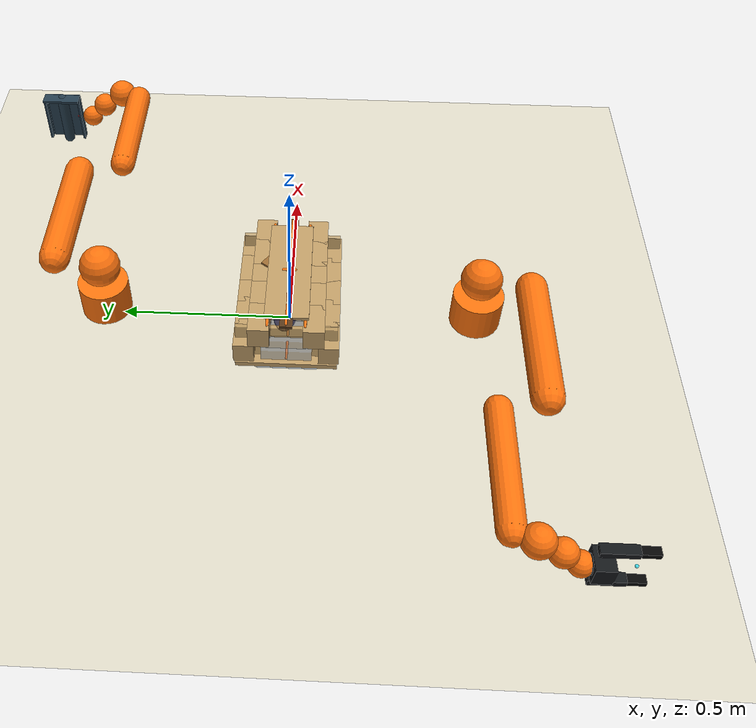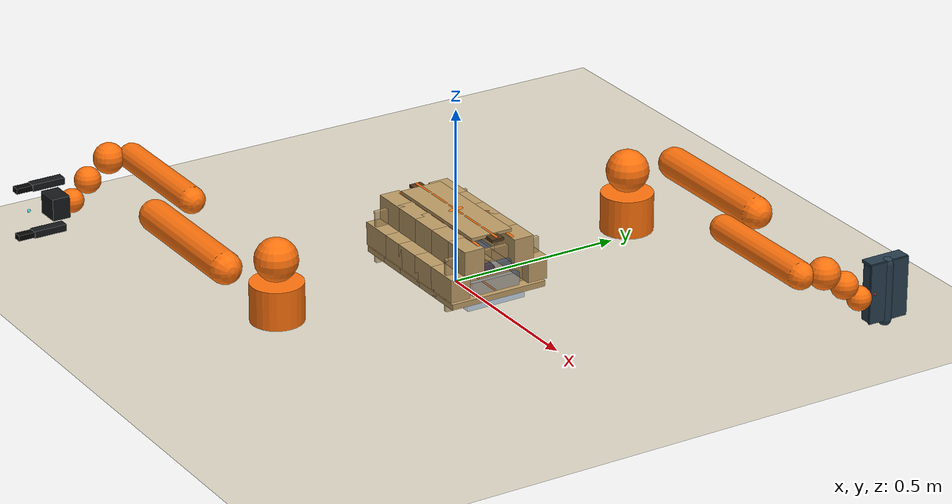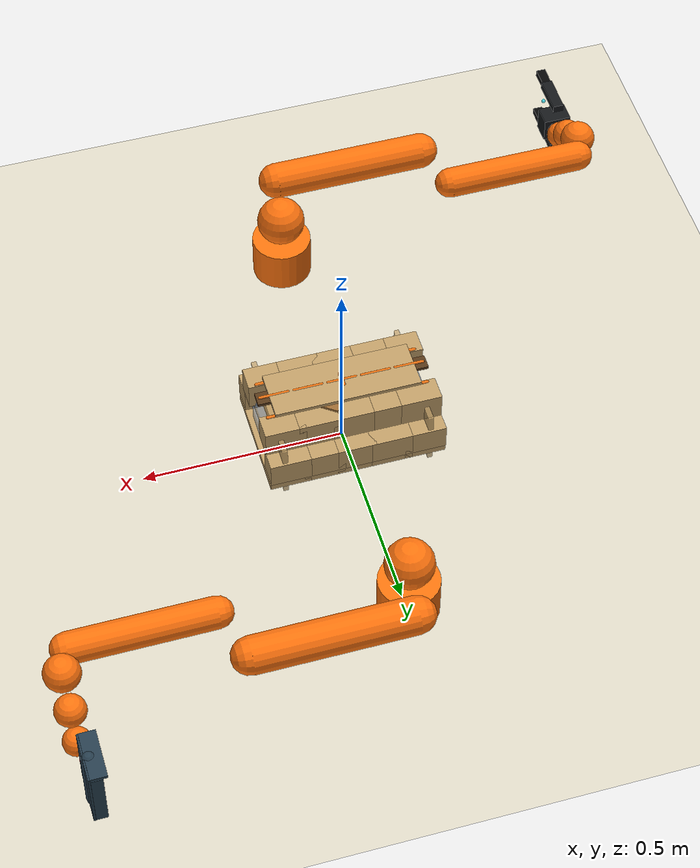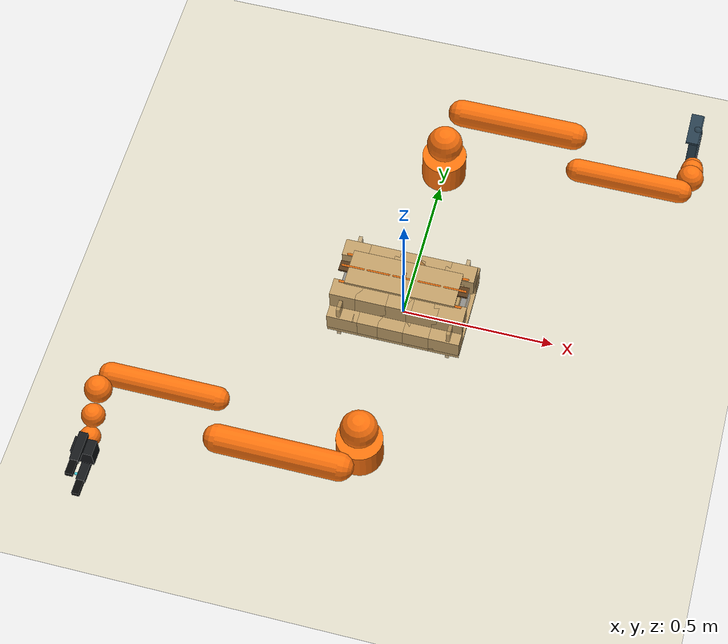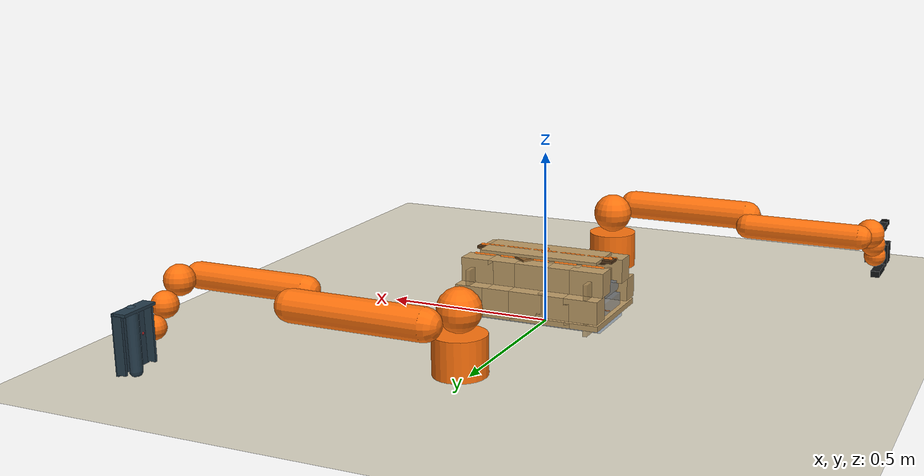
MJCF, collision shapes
<mujoco model="dual_sack_top_fold_simple">
  <compiler angle="degree" autolimits="true" />
  <option timestep="0.001000" gravity="0 0 -9.81" integrator="implicitfast" solver="Newton" iterations="120" ls_iterations="30" jacobian="sparse" cone="elliptic" impratio="4" />
  <size nconmax="3200" njmax="4200" />
  <visual>
    <global offwidth="1280" offheight="820" />
  </visual>
  <asset>
    <mesh name="sealed_pillow_skin_mesh" vertex="-0.210000 -0.120000 0.008250 -0.186667 -0.120000 0.008250 -0.163333 -0.120000 0.008250 -0.140000 -0.120000 0.008250 -0.116667 -0.120000 0.008250 -0.093333 -0.120000 0.008250 -0.070000 -0.120000 0.008250 -0.046667 -0.120000 0.008250 -0.023333 -0.120000 0.008250 0.000000 -0.120000 0.008250 0.023333 -0.120000 0.008250 0.046667 -0.120000 0.008250 0.070000 -0.120000 0.008250 0.093333 -0.120000 0.008250 0.116667 -0.120000 0.008250 0.140000 -0.120000 0.008250 0.163333 -0.120000 0.008250 0.186667 -0.120000 0.008250 0.210000 -0.120000 0.008250 -0.210000 -0.100000 0.008250 -0.186667 -0.100000 0.020123 -0.163333 -0.100000 0.025411 -0.140000 -0.100000 0.025411 -0.116667 -0.100000 0.025411 -0.093333 -0.100000 0.025411 -0.070000 -0.100000 0.025411 -0.046667 -0.100000 0.025411 -0.023333 -0.100000 0.025411 0.000000 -0.100000 0.025411 0.023333 -0.100000 0.025411 0.046667 -0.100000 0.025411 0.070000 -0.100000 0.025411 0.093333 -0.100000 0.025411 0.116667 -0.100000 0.025411 0.140000 -0.100000 0.025411 0.163333 -0.100000 0.025411 0.186667 -0.100000 0.020123 0.210000 -0.100000 0.008250 -0.210000 -0.080000 0.008250 -0.186667 -0.080000 0.020123 -0.163333 -0.080000 0.030277 -0.140000 -0.080000 0.038768 -0.116667 -0.080000 0.038768 -0.093333 -0.080000 0.038768 -0.070000 -0.080000 0.038768 -0.046667 -0.080000 0.038768 -0.023333 -0.080000 0.038768 0.000000 -0.080000 0.038768 0.023333 -0.080000 0.038768 0.046667 -0.080000 0.038768 0.070000 -0.080000 0.038768 0.093333 -0.080000 0.038768 0.116667 -0.080000 0.038768 0.140000 -0.080000 0.038768 0.163333 -0.080000 0.030277 0.186667 -0.080000 0.020123 0.210000 -0.080000 0.008250 -0.210000 -0.060000 0.008250 -0.186667 -0.060000 0.020123 -0.163333 -0.060000 0.030277 -0.140000 -0.060000 0.038768 -0.116667 -0.060000 0.045660 -0.093333 -0.060000 0.048529 -0.070000 -0.060000 0.048529 -0.046667 -0.060000 0.048529 -0.023333 -0.060000 0.048529 0.000000 -0.060000 0.048529 0.023333 -0.060000 0.048529 0.046667 -0.060000 0.048529 0.070000 -0.060000 0.048529 0.093333 -0.060000 0.048529 0.116667 -0.060000 0.045660 0.140000 -0.060000 0.038768 0.163333 -0.060000 0.030277 0.186667 -0.060000 0.020123 0.210000 -0.060000 0.008250 -0.210000 -0.040000 0.008250 -0.186667 -0.040000 0.020123 -0.163333 -0.040000 0.030277 -0.140000 -0.040000 0.038768 -0.116667 -0.040000 0.045660 -0.093333 -0.040000 0.051025 -0.070000 -0.040000 0.054944 -0.046667 -0.040000 0.054944 -0.023333 -0.040000 0.054944 0.000000 -0.040000 0.054944 0.023333 -0.040000 0.054944 0.046667 -0.040000 0.054944 0.070000 -0.040000 0.054944 0.093333 -0.040000 0.051025 0.116667 -0.040000 0.045660 0.140000 -0.040000 0.038768 0.163333 -0.040000 0.030277 0.186667 -0.040000 0.020123 0.210000 -0.040000 0.008250 -0.210000 -0.020000 0.008250 -0.186667 -0.020000 0.020123 -0.163333 -0.020000 0.030277 -0.140000 -0.020000 0.038768 -0.116667 -0.020000 0.045660 -0.093333 -0.020000 0.051025 -0.070000 -0.020000 0.054944 -0.046667 -0.020000 0.057521 -0.023333 -0.020000 0.058345 0.000000 -0.020000 0.058345 0.023333 -0.020000 0.058345 0.046667 -0.020000 0.057521 0.070000 -0.020000 0.054944 0.093333 -0.020000 0.051025 0.116667 -0.020000 0.045660 0.140000 -0.020000 0.038768 0.163333 -0.020000 0.030277 0.186667 -0.020000 0.020123 0.210000 -0.020000 0.008250 -0.210000 0.000000 0.008250 -0.186667 0.000000 0.020123 -0.163333 0.000000 0.030277 -0.140000 0.000000 0.038768 -0.116667 0.000000 0.045660 -0.093333 0.000000 0.051025 -0.070000 0.000000 0.054944 -0.046667 0.000000 0.057521 -0.023333 0.000000 0.058886 0.000000 0.000000 0.059250 0.023333 0.000000 0.058886 0.046667 0.000000 0.057521 0.070000 0.000000 0.054944 0.093333 0.000000 0.051025 0.116667 0.000000 0.045660 0.140000 0.000000 0.038768 0.163333 0.000000 0.030277 0.186667 0.000000 0.020123 0.210000 0.000000 0.008250 -0.210000 0.020000 0.008250 -0.186667 0.020000 0.020123 -0.163333 0.020000 0.030277 -0.140000 0.020000 0.038768 -0.116667 0.020000 0.045660 -0.093333 0.020000 0.051025 -0.070000 0.020000 0.054944 -0.046667 0.020000 0.057521 -0.023333 0.020000 0.058345 0.000000 0.020000 0.058345 0.023333 0.020000 0.058345 0.046667 0.020000 0.057521 0.070000 0.020000 0.054944 0.093333 0.020000 0.051025 0.116667 0.020000 0.045660 0.140000 0.020000 0.038768 0.163333 0.020000 0.030277 0.186667 0.020000 0.020123 0.210000 0.020000 0.008250 -0.210000 0.040000 0.008250 -0.186667 0.040000 0.020123 -0.163333 0.040000 0.030277 -0.140000 0.040000 0.038768 -0.116667 0.040000 0.045660 -0.093333 0.040000 0.051025 -0.070000 0.040000 0.054944 -0.046667 0.040000 0.054944 -0.023333 0.040000 0.054944 0.000000 0.040000 0.054944 0.023333 0.040000 0.054944 0.046667 0.040000 0.054944 0.070000 0.040000 0.054944 0.093333 0.040000 0.051025 0.116667 0.040000 0.045660 0.140000 0.040000 0.038768 0.163333 0.040000 0.030277 0.186667 0.040000 0.020123 0.210000 0.040000 0.008250 -0.210000 0.060000 0.008250 -0.186667 0.060000 0.020123 -0.163333 0.060000 0.030277 -0.140000 0.060000 0.038768 -0.116667 0.060000 0.045660 -0.093333 0.060000 0.048529 -0.070000 0.060000 0.048529 -0.046667 0.060000 0.048529 -0.023333 0.060000 0.048529 0.000000 0.060000 0.048529 0.023333 0.060000 0.048529 0.046667 0.060000 0.048529 0.070000 0.060000 0.048529 0.093333 0.060000 0.048529 0.116667 0.060000 0.045660 0.140000 0.060000 0.038768 0.163333 0.060000 0.030277 0.186667 0.060000 0.020123 0.210000 0.060000 0.008250 -0.210000 0.080000 0.008250 -0.186667 0.080000 0.020123 -0.163333 0.080000 0.030277 -0.140000 0.080000 0.038768 -0.116667 0.080000 0.038768 -0.093333 0.080000 0.038768 -0.070000 0.080000 0.038768 -0.046667 0.080000 0.038768 -0.023333 0.080000 0.038768 0.000000 0.080000 0.038768 0.023333 0.080000 0.038768 0.046667 0.080000 0.038768 0.070000 0.080000 0.038768 0.093333 0.080000 0.038768 0.116667 0.080000 0.038768 0.140000 0.080000 0.038768 0.163333 0.080000 0.030277 0.186667 0.080000 0.020123 0.210000 0.080000 0.008250 -0.210000 0.100000 0.008250 -0.186667 0.100000 0.020123 -0.163333 0.100000 0.025411 -0.140000 0.100000 0.025411 -0.116667 0.100000 0.025411 -0.093333 0.100000 0.025411 -0.070000 0.100000 0.025411 -0.046667 0.100000 0.025411 -0.023333 0.100000 0.025411 0.000000 0.100000 0.025411 0.023333 0.100000 0.025411 0.046667 0.100000 0.025411 0.070000 0.100000 0.025411 0.093333 0.100000 0.025411 0.116667 0.100000 0.025411 0.140000 0.100000 0.025411 0.163333 0.100000 0.025411 0.186667 0.100000 0.020123 0.210000 0.100000 0.008250 -0.210000 0.120000 0.008250 -0.186667 0.120000 0.008250 -0.163333 0.120000 0.008250 -0.140000 0.120000 0.008250 -0.116667 0.120000 0.008250 -0.093333 0.120000 0.008250 -0.070000 0.120000 0.008250 -0.046667 0.120000 0.008250 -0.023333 0.120000 0.008250 0.000000 0.120000 0.008250 0.023333 0.120000 0.008250 0.046667 0.120000 0.008250 0.070000 0.120000 0.008250 0.093333 0.120000 0.008250 0.116667 0.120000 0.008250 0.140000 0.120000 0.008250 0.163333 0.120000 0.008250 0.186667 0.120000 0.008250 0.210000 0.120000 0.008250 -0.210000 -0.120000 -0.008250 -0.186667 -0.120000 -0.008250 -0.163333 -0.120000 -0.008250 -0.140000 -0.120000 -0.008250 -0.116667 -0.120000 -0.008250 -0.093333 -0.120000 -0.008250 -0.070000 -0.120000 -0.008250 -0.046667 -0.120000 -0.008250 -0.023333 -0.120000 -0.008250 0.000000 -0.120000 -0.008250 0.023333 -0.120000 -0.008250 0.046667 -0.120000 -0.008250 0.070000 -0.120000 -0.008250 0.093333 -0.120000 -0.008250 0.116667 -0.120000 -0.008250 0.140000 -0.120000 -0.008250 0.163333 -0.120000 -0.008250 0.186667 -0.120000 -0.008250 0.210000 -0.120000 -0.008250 -0.210000 -0.100000 -0.008250 -0.186667 -0.100000 -0.020123 -0.163333 -0.100000 -0.025411 -0.140000 -0.100000 -0.025411 -0.116667 -0.100000 -0.025411 -0.093333 -0.100000 -0.025411 -0.070000 -0.100000 -0.025411 -0.046667 -0.100000 -0.025411 -0.023333 -0.100000 -0.025411 0.000000 -0.100000 -0.025411 0.023333 -0.100000 -0.025411 0.046667 -0.100000 -0.025411 0.070000 -0.100000 -0.025411 0.093333 -0.100000 -0.025411 0.116667 -0.100000 -0.025411 0.140000 -0.100000 -0.025411 0.163333 -0.100000 -0.025411 0.186667 -0.100000 -0.020123 0.210000 -0.100000 -0.008250 -0.210000 -0.080000 -0.008250 -0.186667 -0.080000 -0.020123 -0.163333 -0.080000 -0.030277 -0.140000 -0.080000 -0.038768 -0.116667 -0.080000 -0.038768 -0.093333 -0.080000 -0.038768 -0.070000 -0.080000 -0.038768 -0.046667 -0.080000 -0.038768 -0.023333 -0.080000 -0.038768 0.000000 -0.080000 -0.038768 0.023333 -0.080000 -0.038768 0.046667 -0.080000 -0.038768 0.070000 -0.080000 -0.038768 0.093333 -0.080000 -0.038768 0.116667 -0.080000 -0.038768 0.140000 -0.080000 -0.038768 0.163333 -0.080000 -0.030277 0.186667 -0.080000 -0.020123 0.210000 -0.080000 -0.008250 -0.210000 -0.060000 -0.008250 -0.186667 -0.060000 -0.020123 -0.163333 -0.060000 -0.030277 -0.140000 -0.060000 -0.038768 -0.116667 -0.060000 -0.045660 -0.093333 -0.060000 -0.048529 -0.070000 -0.060000 -0.048529 -0.046667 -0.060000 -0.048529 -0.023333 -0.060000 -0.048529 0.000000 -0.060000 -0.048529 0.023333 -0.060000 -0.048529 0.046667 -0.060000 -0.048529 0.070000 -0.060000 -0.048529 0.093333 -0.060000 -0.048529 0.116667 -0.060000 -0.045660 0.140000 -0.060000 -0.038768 0.163333 -0.060000 -0.030277 0.186667 -0.060000 -0.020123 0.210000 -0.060000 -0.008250 -0.210000 -0.040000 -0.008250 -0.186667 -0.040000 -0.020123 -0.163333 -0.040000 -0.030277 -0.140000 -0.040000 -0.038768 -0.116667 -0.040000 -0.045660 -0.093333 -0.040000 -0.051025 -0.070000 -0.040000 -0.054944 -0.046667 -0.040000 -0.054944 -0.023333 -0.040000 -0.054944 0.000000 -0.040000 -0.054944 0.023333 -0.040000 -0.054944 0.046667 -0.040000 -0.054944 0.070000 -0.040000 -0.054944 0.093333 -0.040000 -0.051025 0.116667 -0.040000 -0.045660 0.140000 -0.040000 -0.038768 0.163333 -0.040000 -0.030277 0.186667 -0.040000 -0.020123 0.210000 -0.040000 -0.008250 -0.210000 -0.020000 -0.008250 -0.186667 -0.020000 -0.020123 -0.163333 -0.020000 -0.030277 -0.140000 -0.020000 -0.038768 -0.116667 -0.020000 -0.045660 -0.093333 -0.020000 -0.051025 -0.070000 -0.020000 -0.054944 -0.046667 -0.020000 -0.057521 -0.023333 -0.020000 -0.058345 0.000000 -0.020000 -0.058345 0.023333 -0.020000 -0.058345 0.046667 -0.020000 -0.057521 0.070000 -0.020000 -0.054944 0.093333 -0.020000 -0.051025 0.116667 -0.020000 -0.045660 0.140000 -0.020000 -0.038768 0.163333 -0.020000 -0.030277 0.186667 -0.020000 -0.020123 0.210000 -0.020000 -0.008250 -0.210000 0.000000 -0.008250 -0.186667 0.000000 -0.020123 -0.163333 0.000000 -0.030277 -0.140000 0.000000 -0.038768 -0.116667 0.000000 -0.045660 -0.093333 0.000000 -0.051025 -0.070000 0.000000 -0.054944 -0.046667 0.000000 -0.057521 -0.023333 0.000000 -0.058886 0.000000 0.000000 -0.059250 0.023333 0.000000 -0.058886 0.046667 0.000000 -0.057521 0.070000 0.000000 -0.054944 0.093333 0.000000 -0.051025 0.116667 0.000000 -0.045660 0.140000 0.000000 -0.038768 0.163333 0.000000 -0.030277 0.186667 0.000000 -0.020123 0.210000 0.000000 -0.008250 -0.210000 0.020000 -0.008250 -0.186667 0.020000 -0.020123 -0.163333 0.020000 -0.030277 -0.140000 0.020000 -0.038768 -0.116667 0.020000 -0.045660 -0.093333 0.020000 -0.051025 -0.070000 0.020000 -0.054944 -0.046667 0.020000 -0.057521 -0.023333 0.020000 -0.058345 0.000000 0.020000 -0.058345 0.023333 0.020000 -0.058345 0.046667 0.020000 -0.057521 0.070000 0.020000 -0.054944 0.093333 0.020000 -0.051025 0.116667 0.020000 -0.045660 0.140000 0.020000 -0.038768 0.163333 0.020000 -0.030277 0.186667 0.020000 -0.020123 0.210000 0.020000 -0.008250 -0.210000 0.040000 -0.008250 -0.186667 0.040000 -0.020123 -0.163333 0.040000 -0.030277 -0.140000 0.040000 -0.038768 -0.116667 0.040000 -0.045660 -0.093333 0.040000 -0.051025 -0.070000 0.040000 -0.054944 -0.046667 0.040000 -0.054944 -0.023333 0.040000 -0.054944 0.000000 0.040000 -0.054944 0.023333 0.040000 -0.054944 0.046667 0.040000 -0.054944 0.070000 0.040000 -0.054944 0.093333 0.040000 -0.051025 0.116667 0.040000 -0.045660 0.140000 0.040000 -0.038768 0.163333 0.040000 -0.030277 0.186667 0.040000 -0.020123 0.210000 0.040000 -0.008250 -0.210000 0.060000 -0.008250 -0.186667 0.060000 -0.020123 -0.163333 0.060000 -0.030277 -0.140000 0.060000 -0.038768 -0.116667 0.060000 -0.045660 -0.093333 0.060000 -0.048529 -0.070000 0.060000 -0.048529 -0.046667 0.060000 -0.048529 -0.023333 0.060000 -0.048529 0.000000 0.060000 -0.048529 0.023333 0.060000 -0.048529 0.046667 0.060000 -0.048529 0.070000 0.060000 -0.048529 0.093333 0.060000 -0.048529 0.116667 0.060000 -0.045660 0.140000 0.060000 -0.038768 0.163333 0.060000 -0.030277 0.186667 0.060000 -0.020123 0.210000 0.060000 -0.008250 -0.210000 0.080000 -0.008250 -0.186667 0.080000 -0.020123 -0.163333 0.080000 -0.030277 -0.140000 0.080000 -0.038768 -0.116667 0.080000 -0.038768 -0.093333 0.080000 -0.038768 -0.070000 0.080000 -0.038768 -0.046667 0.080000 -0.038768 -0.023333 0.080000 -0.038768 0.000000 0.080000 -0.038768 0.023333 0.080000 -0.038768 0.046667 0.080000 -0.038768 0.070000 0.080000 -0.038768 0.093333 0.080000 -0.038768 0.116667 0.080000 -0.038768 0.140000 0.080000 -0.038768 0.163333 0.080000 -0.030277 0.186667 0.080000 -0.020123 0.210000 0.080000 -0.008250 -0.210000 0.100000 -0.008250 -0.186667 0.100000 -0.020123 -0.163333 0.100000 -0.025411 -0.140000 0.100000 -0.025411 -0.116667 0.100000 -0.025411 -0.093333 0.100000 -0.025411 -0.070000 0.100000 -0.025411 -0.046667 0.100000 -0.025411 -0.023333 0.100000 -0.025411 0.000000 0.100000 -0.025411 0.023333 0.100000 -0.025411 0.046667 0.100000 -0.025411 0.070000 0.100000 -0.025411 0.093333 0.100000 -0.025411 0.116667 0.100000 -0.025411 0.140000 0.100000 -0.025411 0.163333 0.100000 -0.025411 0.186667 0.100000 -0.020123 0.210000 0.100000 -0.008250 -0.210000 0.120000 -0.008250 -0.186667 0.120000 -0.008250 -0.163333 0.120000 -0.008250 -0.140000 0.120000 -0.008250 -0.116667 0.120000 -0.008250 -0.093333 0.120000 -0.008250 -0.070000 0.120000 -0.008250 -0.046667 0.120000 -0.008250 -0.023333 0.120000 -0.008250 0.000000 0.120000 -0.008250 0.023333 0.120000 -0.008250 0.046667 0.120000 -0.008250 0.070000 0.120000 -0.008250 0.093333 0.120000 -0.008250 0.116667 0.120000 -0.008250 0.140000 0.120000 -0.008250 0.163333 0.120000 -0.008250 0.186667 0.120000 -0.008250 0.210000 0.120000 -0.008250" face="0 1 19 1 20 19 247 266 248 248 266 267 1 2 20 2 21 20 248 267 249 249 267 268 2 3 21 3 22 21 249 268 250 250 268 269 3 4 22 4 23 22 250 269 251 251 269 270 4 5 23 5 24 23 251 270 252 252 270 271 5 6 24 6 25 24 252 271 253 253 271 272 6 7 25 7 26 25 253 272 254 254 272 273 7 8 26 8 27 26 254 273 255 255 273 274 8 9 27 9 28 27 255 274 256 256 274 275 9 10 28 10 29 28 256 275 257 257 275 276 10 11 29 11 30 29 257 276 258 258 276 277 11 12 30 12 31 30 258 277 259 259 277 278 12 13 31 13 32 31 259 278 260 260 278 279 13 14 32 14 33 32 260 279 261 261 279 280 14 15 33 15 34 33 261 280 262 262 280 281 15 16 34 16 35 34 262 281 263 263 281 282 16 17 35 17 36 35 263 282 264 264 282 283 17 18 36 18 37 36 264 283 265 265 283 284 19 20 38 20 39 38 266 285 267 267 285 286 20 21 39 21 40 39 267 286 268 268 286 287 21 22 40 22 41 40 268 287 269 269 287 288 22 23 41 23 42 41 269 288 270 270 288 289 23 24 42 24 43 42 270 289 271 271 289 290 24 25 43 25 44 43 271 290 272 272 290 291 25 26 44 26 45 44 272 291 273 273 291 292 26 27 45 27 46 45 273 292 274 274 292 293 27 28 46 28 47 46 274 293 275 275 293 294 28 29 47 29 48 47 275 294 276 276 294 295 29 30 48 30 49 48 276 295 277 277 295 296 30 31 49 31 50 49 277 296 278 278 296 297 31 32 50 32 51 50 278 297 279 279 297 298 32 33 51 33 52 51 279 298 280 280 298 299 33 34 52 34 53 52 280 299 281 281 299 300 34 35 53 35 54 53 281 300 282 282 300 301 35 36 54 36 55 54 282 301 283 283 301 302 36 37 55 37 56 55 283 302 284 284 302 303 38 39 57 39 58 57 285 304 286 286 304 305 39 40 58 40 59 58 286 305 287 287 305 306 40 41 59 41 60 59 287 306 288 288 306 307 41 42 60 42 61 60 288 307 289 289 307 308 42 43 61 43 62 61 289 308 290 290 308 309 43 44 62 44 63 62 290 309 291 291 309 310 44 45 63 45 64 63 291 310 292 292 310 311 45 46 64 46 65 64 292 311 293 293 311 312 46 47 65 47 66 65 293 312 294 294 312 313 47 48 66 48 67 66 294 313 295 295 313 314 48 49 67 49 68 67 295 314 296 296 314 315 49 50 68 50 69 68 296 315 297 297 315 316 50 51 69 51 70 69 297 316 298 298 316 317 51 52 70 52 71 70 298 317 299 299 317 318 52 53 71 53 72 71 299 318 300 300 318 319 53 54 72 54 73 72 300 319 301 301 319 320 54 55 73 55 74 73 301 320 302 302 320 321 55 56 74 56 75 74 302 321 303 303 321 322 57 58 76 58 77 76 304 323 305 305 323 324 58 59 77 59 78 77 305 324 306 306 324 325 59 60 78 60 79 78 306 325 307 307 325 326 60 61 79 61 80 79 307 326 308 308 326 327 61 62 80 62 81 80 308 327 309 309 327 328 62 63 81 63 82 81 309 328 310 310 328 329 63 64 82 64 83 82 310 329 311 311 329 330 64 65 83 65 84 83 311 330 312 312 330 331 65 66 84 66 85 84 312 331 313 313 331 332 66 67 85 67 86 85 313 332 314 314 332 333 67 68 86 68 87 86 314 333 315 315 333 334 68 69 87 69 88 87 315 334 316 316 334 335 69 70 88 70 89 88 316 335 317 317 335 336 70 71 89 71 90 89 317 336 318 318 336 337 71 72 90 72 91 90 318 337 319 319 337 338 72 73 91 73 92 91 319 338 320 320 338 339 73 74 92 74 93 92 320 339 321 321 339 340 74 75 93 75 94 93 321 340 322 322 340 341 76 77 95 77 96 95 323 342 324 324 342 343 77 78 96 78 97 96 324 343 325 325 343 344 78 79 97 79 98 97 325 344 326 326 344 345 79 80 98 80 99 98 326 345 327 327 345 346 80 81 99 81 100 99 327 346 328 328 346 347 81 82 100 82 101 100 328 347 329 329 347 348 82 83 101 83 102 101 329 348 330 330 348 349 83 84 102 84 103 102 330 349 331 331 349 350 84 85 103 85 104 103 331 350 332 332 350 351 85 86 104 86 105 104 332 351 333 333 351 352 86 87 105 87 106 105 333 352 334 334 352 353 87 88 106 88 107 106 334 353 335 335 353 354 88 89 107 89 108 107 335 354 336 336 354 355 89 90 108 90 109 108 336 355 337 337 355 356 90 91 109 91 110 109 337 356 338 338 356 357 91 92 110 92 111 110 338 357 339 339 357 358 92 93 111 93 112 111 339 358 340 340 358 359 93 94 112 94 113 112 340 359 341 341 359 360 95 96 114 96 115 114 342 361 343 343 361 362 96 97 115 97 116 115 343 362 344 344 362 363 97 98 116 98 117 116 344 363 345 345 363 364 98 99 117 99 118 117 345 364 346 346 364 365 99 100 118 100 119 118 346 365 347 347 365 366 100 101 119 101 120 119 347 366 348 348 366 367 101 102 120 102 121 120 348 367 349 349 367 368 102 103 121 103 122 121 349 368 350 350 368 369 103 104 122 104 123 122 350 369 351 351 369 370 104 105 123 105 124 123 351 370 352 352 370 371 105 106 124 106 125 124 352 371 353 353 371 372 106 107 125 107 126 125 353 372 354 354 372 373 107 108 126 108 127 126 354 373 355 355 373 374 108 109 127 109 128 127 355 374 356 356 374 375 109 110 128 110 129 128 356 375 357 357 375 376 110 111 129 111 130 129 357 376 358 358 376 377 111 112 130 112 131 130 358 377 359 359 377 378 112 113 131 113 132 131 359 378 360 360 378 379 114 115 133 115 134 133 361 380 362 362 380 381 115 116 134 116 135 134 362 381 363 363 381 382 116 117 135 117 136 135 363 382 364 364 382 383 117 118 136 118 137 136 364 383 365 365 383 384 118 119 137 119 138 137 365 384 366 366 384 385 119 120 138 120 139 138 366 385 367 367 385 386 120 121 139 121 140 139 367 386 368 368 386 387 121 122 140 122 141 140 368 387 369 369 387 388 122 123 141 123 142 141 369 388 370 370 388 389 123 124 142 124 143 142 370 389 371 371 389 390 124 125 143 125 144 143 371 390 372 372 390 391 125 126 144 126 145 144 372 391 373 373 391 392 126 127 145 127 146 145 373 392 374 374 392 393 127 128 146 128 147 146 374 393 375 375 393 394 128 129 147 129 148 147 375 394 376 376 394 395 129 130 148 130 149 148 376 395 377 377 395 396 130 131 149 131 150 149 377 396 378 378 396 397 131 132 150 132 151 150 378 397 379 379 397 398 133 134 152 134 153 152 380 399 381 381 399 400 134 135 153 135 154 153 381 400 382 382 400 401 135 136 154 136 155 154 382 401 383 383 401 402 136 137 155 137 156 155 383 402 384 384 402 403 137 138 156 138 157 156 384 403 385 385 403 404 138 139 157 139 158 157 385 404 386 386 404 405 139 140 158 140 159 158 386 405 387 387 405 406 140 141 159 141 160 159 387 406 388 388 406 407 141 142 160 142 161 160 388 407 389 389 407 408 142 143 161 143 162 161 389 408 390 390 408 409 143 144 162 144 163 162 390 409 391 391 409 410 144 145 163 145 164 163 391 410 392 392 410 411 145 146 164 146 165 164 392 411 393 393 411 412 146 147 165 147 166 165 393 412 394 394 412 413 147 148 166 148 167 166 394 413 395 395 413 414 148 149 167 149 168 167 395 414 396 396 414 415 149 150 168 150 169 168 396 415 397 397 415 416 150 151 169 151 170 169 397 416 398 398 416 417 152 153 171 153 172 171 399 418 400 400 418 419 153 154 172 154 173 172 400 419 401 401 419 420 154 155 173 155 174 173 401 420 402 402 420 421 155 156 174 156 175 174 402 421 403 403 421 422 156 157 175 157 176 175 403 422 404 404 422 423 157 158 176 158 177 176 404 423 405 405 423 424 158 159 177 159 178 177 405 424 406 406 424 425 159 160 178 160 179 178 406 425 407 407 425 426 160 161 179 161 180 179 407 426 408 408 426 427 161 162 180 162 181 180 408 427 409 409 427 428 162 163 181 163 182 181 409 428 410 410 428 429 163 164 182 164 183 182 410 429 411 411 429 430 164 165 183 165 184 183 411 430 412 412 430 431 165 166 184 166 185 184 412 431 413 413 431 432 166 167 185 167 186 185 413 432 414 414 432 433 167 168 186 168 187 186 414 433 415 415 433 434 168 169 187 169 188 187 415 434 416 416 434 435 169 170 188 170 189 188 416 435 417 417 435 436 171 172 190 172 191 190 418 437 419 419 437 438 172 173 191 173 192 191 419 438 420 420 438 439 173 174 192 174 193 192 420 439 421 421 439 440 174 175 193 175 194 193 421 440 422 422 440 441 175 176 194 176 195 194 422 441 423 423 441 442 176 177 195 177 196 195 423 442 424 424 442 443 177 178 196 178 197 196 424 443 425 425 443 444 178 179 197 179 198 197 425 444 426 426 444 445 179 180 198 180 199 198 426 445 427 427 445 446 180 181 199 181 200 199 427 446 428 428 446 447 181 182 200 182 201 200 428 447 429 429 447 448 182 183 201 183 202 201 429 448 430 430 448 449 183 184 202 184 203 202 430 449 431 431 449 450 184 185 203 185 204 203 431 450 432 432 450 451 185 186 204 186 205 204 432 451 433 433 451 452 186 187 205 187 206 205 433 452 434 434 452 453 187 188 206 188 207 206 434 453 435 435 453 454 188 189 207 189 208 207 435 454 436 436 454 455 190 191 209 191 210 209 437 456 438 438 456 457 191 192 210 192 211 210 438 457 439 439 457 458 192 193 211 193 212 211 439 458 440 440 458 459 193 194 212 194 213 212 440 459 441 441 459 460 194 195 213 195 214 213 441 460 442 442 460 461 195 196 214 196 215 214 442 461 443 443 461 462 196 197 215 197 216 215 443 462 444 444 462 463 197 198 216 198 217 216 444 463 445 445 463 464 198 199 217 199 218 217 445 464 446 446 464 465 199 200 218 200 219 218 446 465 447 447 465 466 200 201 219 201 220 219 447 466 448 448 466 467 201 202 220 202 221 220 448 467 449 449 467 468 202 203 221 203 222 221 449 468 450 450 468 469 203 204 222 204 223 222 450 469 451 451 469 470 204 205 223 205 224 223 451 470 452 452 470 471 205 206 224 206 225 224 452 471 453 453 471 472 206 207 225 207 226 225 453 472 454 454 472 473 207 208 226 208 227 226 454 473 455 455 473 474 209 210 228 210 229 228 456 475 457 457 475 476 210 211 229 211 230 229 457 476 458 458 476 477 211 212 230 212 231 230 458 477 459 459 477 478 212 213 231 213 232 231 459 478 460 460 478 479 213 214 232 214 233 232 460 479 461 461 479 480 214 215 233 215 234 233 461 480 462 462 480 481 215 216 234 216 235 234 462 481 463 463 481 482 216 217 235 217 236 235 463 482 464 464 482 483 217 218 236 218 237 236 464 483 465 465 483 484 218 219 237 219 238 237 465 484 466 466 484 485 219 220 238 220 239 238 466 485 467 467 485 486 220 221 239 221 240 239 467 486 468 468 486 487 221 222 240 222 241 240 468 487 469 469 487 488 222 223 241 223 242 241 469 488 470 470 488 489 223 224 242 224 243 242 470 489 471 471 489 490 224 225 243 225 244 243 471 490 472 472 490 491 225 226 244 226 245 244 472 491 473 473 491 492 226 227 245 227 246 245 473 492 474 474 492 493 0 247 1 1 247 248 228 229 475 229 476 475 1 248 2 2 248 249 229 230 476 230 477 476 2 249 3 3 249 250 230 231 477 231 478 477 3 250 4 4 250 251 231 232 478 232 479 478 4 251 5 5 251 252 232 233 479 233 480 479 5 252 6 6 252 253 233 234 480 234 481 480 6 253 7 7 253 254 234 235 481 235 482 481 7 254 8 8 254 255 235 236 482 236 483 482 8 255 9 9 255 256 236 237 483 237 484 483 9 256 10 10 256 257 237 238 484 238 485 484 10 257 11 11 257 258 238 239 485 239 486 485 11 258 12 12 258 259 239 240 486 240 487 486 12 259 13 13 259 260 240 241 487 241 488 487 13 260 14 14 260 261 241 242 488 242 489 488 14 261 15 15 261 262 242 243 489 243 490 489 15 262 16 16 262 263 243 244 490 244 491 490 16 263 17 17 263 264 244 245 491 245 492 491 17 264 18 18 264 265 245 246 492 246 493 492 0 19 247 19 266 247 18 265 37 37 265 284 19 38 266 38 285 266 37 284 56 56 284 303 38 57 285 57 304 285 56 303 75 75 303 322 57 76 304 76 323 304 75 322 94 94 322 341 76 95 323 95 342 323 94 341 113 113 341 360 95 114 342 114 361 342 113 360 132 132 360 379 114 133 361 133 380 361 132 379 151 151 379 398 133 152 380 152 399 380 151 398 170 170 398 417 152 171 399 171 418 399 170 417 189 189 417 436 171 190 418 190 437 418 189 436 208 208 436 455 190 209 437 209 456 437 208 455 227 227 455 474 209 228 456 228 475 456 227 474 246 246 474 493" />
    <material name="mat_jute" rgba="0.72 0.58 0.36 0.22" />
    <material name="mat_shell_panel" rgba="0.70 0.55 0.31 0.94" />
    <material name="mat_connected_shell" rgba="0.74 0.61 0.40 0.97" />
    <material name="mat_connected_edge" rgba="0.46 0.32 0.17 0.96" />
    <material name="mat_panel_hidden" rgba="0.70 0.55 0.31 0.94" />
    <material name="mat_hinge_cylinder" rgba="0.43 0.28 0.13 0.95" />
    <material name="mat_seam" rgba="0.34 0.22 0.10 0.88" />
    <material name="mat_fold" rgba="0.66 0.46 0.22 0.82" />
    <material name="mat_inner_shell" rgba="0.18 0.42 0.78 0.34" />
    <material name="mat_ballast" rgba="0.30 0.13 0.06 0.26" />
    <material name="mat_payload" rgba="0.30 0.13 0.06 0.20" />
    <material name="mat_ur5_base" rgba="0.26 0.30 0.34 1" />
    <material name="mat_ur5_link" rgba="0.74 0.78 0.80 1" />
    <material name="mat_ur5_joint_marker" rgba="1.00 0.48 0.08 1" />
    <material name="mat_gripper" rgba="0.08 0.09 0.10 1" />
    <material name="mat_pad" rgba="0.02 0.02 0.02 1" />
    <material name="mat_scoop" rgba="0.15 0.24 0.30 1" />
    <material name="mat_ur5e_black" rgba="0.033 0.033 0.033 1" specular="0.5" shininess="0.25" />
    <material name="mat_ur5e_jointgray" rgba="0.278 0.278 0.278 1" specular="0.5" shininess="0.25" />
    <material name="mat_ur5e_linkgray" rgba="0.82 0.82 0.82 1" specular="0.5" shininess="0.25" />
    <material name="mat_ur5e_urblue" rgba="0.49 0.678 0.8 1" specular="0.5" shininess="0.25" />
    <mesh name="ur5e_base_0" file="D:\Michael\2025\01.Research\01.Parceldetection\16.Pybullet\mujoco_menagerie\universal_robots_ur5e\assets\base_0.obj" />
    <mesh name="ur5e_base_1" file="D:\Michael\2025\01.Research\01.Parceldetection\16.Pybullet\mujoco_menagerie\universal_robots_ur5e\assets\base_1.obj" />
    <mesh name="ur5e_shoulder_0" file="D:\Michael\2025\01.Research\01.Parceldetection\16.Pybullet\mujoco_menagerie\universal_robots_ur5e\assets\shoulder_0.obj" />
    <mesh name="ur5e_shoulder_1" file="D:\Michael\2025\01.Research\01.Parceldetection\16.Pybullet\mujoco_menagerie\universal_robots_ur5e\assets\shoulder_1.obj" />
    <mesh name="ur5e_shoulder_2" file="D:\Michael\2025\01.Research\01.Parceldetection\16.Pybullet\mujoco_menagerie\universal_robots_ur5e\assets\shoulder_2.obj" />
    <mesh name="ur5e_upperarm_0" file="D:\Michael\2025\01.Research\01.Parceldetection\16.Pybullet\mujoco_menagerie\universal_robots_ur5e\assets\upperarm_0.obj" />
    <mesh name="ur5e_upperarm_1" file="D:\Michael\2025\01.Research\01.Parceldetection\16.Pybullet\mujoco_menagerie\universal_robots_ur5e\assets\upperarm_1.obj" />
    <mesh name="ur5e_upperarm_2" file="D:\Michael\2025\01.Research\01.Parceldetection\16.Pybullet\mujoco_menagerie\universal_robots_ur5e\assets\upperarm_2.obj" />
    <mesh name="ur5e_upperarm_3" file="D:\Michael\2025\01.Research\01.Parceldetection\16.Pybullet\mujoco_menagerie\universal_robots_ur5e\assets\upperarm_3.obj" />
    <mesh name="ur5e_forearm_0" file="D:\Michael\2025\01.Research\01.Parceldetection\16.Pybullet\mujoco_menagerie\universal_robots_ur5e\assets\forearm_0.obj" />
    <mesh name="ur5e_forearm_1" file="D:\Michael\2025\01.Research\01.Parceldetection\16.Pybullet\mujoco_menagerie\universal_robots_ur5e\assets\forearm_1.obj" />
    <mesh name="ur5e_forearm_2" file="D:\Michael\2025\01.Research\01.Parceldetection\16.Pybullet\mujoco_menagerie\universal_robots_ur5e\assets\forearm_2.obj" />
    <mesh name="ur5e_forearm_3" file="D:\Michael\2025\01.Research\01.Parceldetection\16.Pybullet\mujoco_menagerie\universal_robots_ur5e\assets\forearm_3.obj" />
    <mesh name="ur5e_wrist1_0" file="D:\Michael\2025\01.Research\01.Parceldetection\16.Pybullet\mujoco_menagerie\universal_robots_ur5e\assets\wrist1_0.obj" />
    <mesh name="ur5e_wrist1_1" file="D:\Michael\2025\01.Research\01.Parceldetection\16.Pybullet\mujoco_menagerie\universal_robots_ur5e\assets\wrist1_1.obj" />
    <mesh name="ur5e_wrist1_2" file="D:\Michael\2025\01.Research\01.Parceldetection\16.Pybullet\mujoco_menagerie\universal_robots_ur5e\assets\wrist1_2.obj" />
    <mesh name="ur5e_wrist2_0" file="D:\Michael\2025\01.Research\01.Parceldetection\16.Pybullet\mujoco_menagerie\universal_robots_ur5e\assets\wrist2_0.obj" />
    <mesh name="ur5e_wrist2_1" file="D:\Michael\2025\01.Research\01.Parceldetection\16.Pybullet\mujoco_menagerie\universal_robots_ur5e\assets\wrist2_1.obj" />
    <mesh name="ur5e_wrist2_2" file="D:\Michael\2025\01.Research\01.Parceldetection\16.Pybullet\mujoco_menagerie\universal_robots_ur5e\assets\wrist2_2.obj" />
    <mesh name="ur5e_wrist3" file="D:\Michael\2025\01.Research\01.Parceldetection\16.Pybullet\mujoco_menagerie\universal_robots_ur5e\assets\wrist3.obj" />
  </asset>
  <worldbody>
    <geom group="0" condim="4" friction="1.55 0.05 0.004" solref="0.028 1" solimp="0.76 0.94 0.001" name="floor" type="plane" size="2.4 2.4 0.05" rgba="0.86 0.84 0.77 0.55" />
    <light name="key_light" pos="0.5 -0.7 1.3" dir="-0.25 0.3 -1" />
    <light name="fill_light" pos="-0.6 0.5 0.9" dir="0.4 -0.2 -1" diffuse="0.35 0.32 0.28" />
    <camera name="front" pos="0.58 -0.66 0.32" xyaxes="0.76 0.65 0 -0.20 0.23 0.95" />
    <camera name="side" pos="0.78 0.00 0.25" xyaxes="0 1 0 -0.18 0 0.98" />
    <camera name="longitudinal_end" pos="0.70 0.00 0.20" xyaxes="0 1 0 -0.16 0 0.99" />
    <camera name="top_angle" pos="0.38 -0.48 0.58" xyaxes="0.78 0.62 0 -0.50 0.63 0.59" />
    <camera name="dual" pos="1.95 -2.35 1.25" xyaxes="0.78 0.63 0 -0.35 0.43 0.83" fovy="75" />
    <body name="bag_frame" pos="0 0 0.105000" euler="0.000000 0 0">
      <freejoint name="bag_frame_freejoint" />
      <site name="site_bag_frame" pos="0 0 0" size="0.0005" rgba="1 0 0 0.00" />
      <body name="visual_skin" pos="0 0 0">
        <geom group="3" condim="4" friction="1.35 0.06 0.006" solref="0.028 1" solimp="0.76 0.94 0.001" name="visual_skin_main" type="mesh" mesh="sealed_pillow_skin_mesh" material="mat_jute" contype="0" conaffinity="0" mass="0.001" />
        <body name="sealed_top_cap_visual" pos="0 0 0.081000">
          <geom group="3" condim="4" friction="1.35 0.06 0.006" solref="0.028 1" solimp="0.76 0.94 0.001" name="sealed_top_cap_visual_geom" type="box" size="0.117600 0.007200 0.0025" rgba="0.50 0.34 0.16 0.18" contype="0" conaffinity="0" mass="0.001" />
        </body>
        <body name="left_end_cap_visual" pos="-0.180600 0 -0.010000">
          <geom group="1" condim="4" friction="1.35 0.06 0.006" solref="0.028 1" solimp="0.76 0.94 0.001" name="left_end_cap_visual_geom" type="box" size="0.006000 0.144000 0.075000" material="mat_connected_shell" rgba="0.74 0.61 0.40 0.72" contype="0" conaffinity="0" mass="0.001" />
          <site name="site_left_end_cap_visual" pos="0 0 0" size="0.0008" rgba="1 0.9 0.2 0.00" />
        </body>
        <body name="right_end_cap_visual" pos="0.180600 0 -0.010000">
          <geom group="1" condim="4" friction="1.35 0.06 0.006" solref="0.028 1" solimp="0.76 0.94 0.001" name="right_end_cap_visual_geom" type="box" size="0.006000 0.144000 0.075000" material="mat_connected_shell" rgba="0.74 0.61 0.40 0.72" contype="0" conaffinity="0" mass="0.001" />
          <site name="site_right_end_cap_visual" pos="0 0 0" size="0.0008" rgba="1 0.9 0.2 0.00" />
        </body>
        <body name="visual_print_mark" pos="-0.04 -0.01 0.044" euler="0 0 -4">
          <geom group="3" condim="4" friction="1.35 0.06 0.006" solref="0.028 1" solimp="0.76 0.94 0.001" name="visual_print_mark_geom" type="box" size="0.055 0.007 0.001" rgba="0.07 0.06 0.05 0.18" contype="0" conaffinity="0" mass="0.001" />
        </body>
      </body>
      <body name="visible_articulated_outer_shell" pos="0 0 0">
        <body name="top_grasp_rail" pos="0.000000 0.000000 0.093000">
          <joint damping="0.50000" stiffness="0.07000" limited="true" name="top_grasp_rail_pitch" type="hinge" axis="0 1 0" range="-28.000 28.000" springref="0.000000" />
          <geom group="1" condim="4" friction="1.55 0.08 0.008" solref="0.028 1" solimp="0.76 0.94 0.001" name="top_grasp_rail_geom" type="capsule" fromto="-0.180600 0 0 0.180600 0 0" size="0.0080" material="mat_seam" mass="0.035" contype="2" conaffinity="5" />
          <geom group="1" condim="4" friction="1.35 0.06 0.006" solref="0.028 1" solimp="0.76 0.94 0.001" name="joint_axis_top_grasp_rail_pitch" type="capsule" fromto="0 -0.016800 0.013 0 0.016800 0.013" size="0.004800" material="mat_ur5_joint_marker" contype="0" conaffinity="0" mass="0.001" />
          <geom group="1" condim="4" friction="1.45 0.06 0.006" solref="0.028 1" solimp="0.76 0.94 0.001" name="sealed_top_cap_cross_section_geom" type="box" pos="0.000000 0.000000 0.009000" size="0.180600 0.062304 0.004500" material="mat_connected_shell" mass="0.0260" contype="2" conaffinity="5" />
          <site name="site_top_grasp_rail_center" pos="0 0 0.012" size="0.002" rgba="1 0.2 0.1 0.65" />
          <body name="slice_00_left_end" pos="-0.168000 0 0">
            <body name="top_seam_band_00" pos="0.000000 0.000000 0.002000">
              <joint damping="0.46000" stiffness="0.08500" limited="true" name="top_seam_band_00_hinge" type="hinge" axis="0 1 0" range="-36.000 36.000" springref="0.000000" />
              <geom group="1" condim="4" friction="1.35 0.06 0.006" solref="0.028 1" solimp="0.76 0.94 0.001" name="joint_axis_top_seam_band_00" type="capsule" fromto="-0.035280 0 0.010 0.035280 0 0.010" size="0.003400" material="mat_ur5_joint_marker" contype="0" conaffinity="0" mass="0.001" />
              <geom group="1" condim="4" friction="1.45 0.06 0.006" solref="0.028 1" solimp="0.76 0.94 0.001" name="top_seam_band_00_geom" type="box" pos="0.000000 0.000000 0.004000" size="0.043680 0.018000 0.004000" material="mat_seam" mass="0.0100" contype="2" conaffinity="5" />
              <site name="site_top_seam_00" pos="0 0 0.014" size="0.0008" rgba="0.1 0.35 1 0.00" />
              <site name="site_top_seam_left" pos="0 0 0.017" size="0.0008" rgba="0.1 0.35 1 0.00" />
              <body name="upper_left_00" pos="0.000000 0.052800 -0.004000">
                <joint damping="0.68000" stiffness="0.14000" limited="true" name="upper_left_00_hinge" type="hinge" axis="1 0 0" range="-48.000 48.000" springref="0.000000" />
                <geom group="1" condim="4" friction="1.35 0.06 0.006" solref="0.028 1" solimp="0.76 0.94 0.001" name="joint_axis_upper_left_00" type="capsule" fromto="-0.030240 0 0 0.030240 0 0" size="0.004000" material="mat_ur5_joint_marker" contype="0" conaffinity="0" mass="0.001" />
                <geom group="1" condim="4" friction="1.45 0.06 0.006" solref="0.028 1" solimp="0.76 0.94 0.001" name="upper_left_00_geom" type="box" pos="0.000000 0.024000 -0.035000" size="0.050400 0.030000 0.035000" material="mat_connected_shell" mass="0.0340" contype="2" conaffinity="5" />
                <site name="site_upper_left_00" pos="0 0.048000 -0.070000" size="0.0007" rgba="0.2 0.8 1 0.00" />
                <site name="site_shoulder_left_00" pos="0 0.048000 -0.070000" size="0.0007" rgba="0.2 0.8 1 0.00" />
                <body name="lower_left_00" pos="0.000000 0.048000 -0.070000">
                  <joint damping="0.44000" stiffness="0.13000" limited="true" name="lower_left_00_hinge" type="hinge" axis="1 0 0" range="-62.000 62.000" springref="0.000000" />
                  <geom group="1" condim="4" friction="1.35 0.06 0.006" solref="0.028 1" solimp="0.76 0.94 0.001" name="joint_axis_lower_left_00" type="capsule" fromto="-0.030240 0 0 0.030240 0 0" size="0.003800" material="mat_ur5_joint_marker" contype="0" conaffinity="0" mass="0.001" />
                  <geom group="1" condim="4" friction="1.45 0.06 0.006" solref="0.028 1" solimp="0.76 0.94 0.001" name="lower_left_00_geom" type="box" pos="0.000000 0.019200 -0.033000" size="0.050400 0.029200 0.033000" material="mat_connected_shell" mass="0.0400" contype="2" conaffinity="5" />
                  <site name="site_lower_left_00" pos="0 0.038400 -0.066000" size="0.0007" rgba="0.2 0.8 1 0.00" />
                  <site name="site_bottom_edge_left_00" pos="0 0.038400 -0.078000" size="0.0007" rgba="1 0.5 0.1 0.00" />
                </body>
              </body>
              <body name="upper_right_00" pos="0.000000 -0.052800 -0.004000">
                <joint damping="0.68000" stiffness="0.14000" limited="true" name="upper_right_00_hinge" type="hinge" axis="1 0 0" range="-48.000 48.000" springref="-0.000000" />
                <geom group="1" condim="4" friction="1.35 0.06 0.006" solref="0.028 1" solimp="0.76 0.94 0.001" name="joint_axis_upper_right_00" type="capsule" fromto="-0.030240 0 0 0.030240 0 0" size="0.004000" material="mat_ur5_joint_marker" contype="0" conaffinity="0" mass="0.001" />
                <geom group="1" condim="4" friction="1.45 0.06 0.006" solref="0.028 1" solimp="0.76 0.94 0.001" name="upper_right_00_geom" type="box" pos="0.000000 -0.024000 -0.035000" size="0.050400 0.030000 0.035000" material="mat_connected_shell" mass="0.0340" contype="2" conaffinity="5" />
                <site name="site_upper_right_00" pos="0 -0.048000 -0.070000" size="0.0007" rgba="0.2 0.8 1 0.00" />
                <site name="site_shoulder_right_00" pos="0 -0.048000 -0.070000" size="0.0007" rgba="0.2 0.8 1 0.00" />
                <body name="lower_right_00" pos="0.000000 -0.048000 -0.070000">
                  <joint damping="0.44000" stiffness="0.13000" limited="true" name="lower_right_00_hinge" type="hinge" axis="1 0 0" range="-62.000 62.000" springref="-0.000000" />
                  <geom group="1" condim="4" friction="1.35 0.06 0.006" solref="0.028 1" solimp="0.76 0.94 0.001" name="joint_axis_lower_right_00" type="capsule" fromto="-0.030240 0 0 0.030240 0 0" size="0.003800" material="mat_ur5_joint_marker" contype="0" conaffinity="0" mass="0.001" />
                  <geom group="1" condim="4" friction="1.45 0.06 0.006" solref="0.028 1" solimp="0.76 0.94 0.001" name="lower_right_00_geom" type="box" pos="0.000000 -0.019200 -0.033000" size="0.050400 0.029200 0.033000" material="mat_connected_shell" mass="0.0400" contype="2" conaffinity="5" />
                  <site name="site_lower_right_00" pos="0 -0.038400 -0.066000" size="0.0007" rgba="0.2 0.8 1 0.00" />
                  <site name="site_bottom_edge_right_00" pos="0 -0.038400 -0.078000" size="0.0007" rgba="1 0.5 0.1 0.00" />
                </body>
              </body>
            </body>
            <body name="bottom_00" pos="0.000000 0.000000 -0.146000">
              <joint damping="0.34000" stiffness="0.05200" limited="true" name="bottom_00_hinge" type="hinge" axis="0 1 0" range="-70.000 70.000" springref="0.000000" />
              <geom group="1" condim="4" friction="1.35 0.06 0.006" solref="0.028 1" solimp="0.76 0.94 0.001" name="joint_axis_bottom_00" type="capsule" fromto="-0.030240 0 0 0.030240 0 0" size="0.003800" material="mat_ur5_joint_marker" contype="0" conaffinity="0" mass="0.001" />
              <geom group="1" condim="4" friction="1.45 0.06 0.006" solref="0.028 1" solimp="0.76 0.94 0.001" name="bottom_00_geom" type="box" pos="0.000000 0.000000 -0.006000" size="0.050400 0.144768 0.008000" material="mat_connected_shell" mass="0.0420" contype="2" conaffinity="5" />
              <site name="site_bottom_00" pos="0 0 -0.016" size="0.0007" rgba="1 0.5 0.1 0.00" />
            </body>
          </body>
          <body name="slice_01_left_mid" pos="-0.084000 0 0">
            <body name="top_seam_band_01" pos="0.000000 0.000000 0.002000">
              <joint damping="0.46000" stiffness="0.08500" limited="true" name="top_seam_band_01_hinge" type="hinge" axis="0 1 0" range="-36.000 36.000" springref="0.000000" />
              <geom group="1" condim="4" friction="1.35 0.06 0.006" solref="0.028 1" solimp="0.76 0.94 0.001" name="joint_axis_top_seam_band_01" type="capsule" fromto="-0.035280 0 0.010 0.035280 0 0.010" size="0.003400" material="mat_ur5_joint_marker" contype="0" conaffinity="0" mass="0.001" />
              <geom group="1" condim="4" friction="1.45 0.06 0.006" solref="0.028 1" solimp="0.76 0.94 0.001" name="top_seam_band_01_geom" type="box" pos="0.000000 0.000000 0.004000" size="0.043680 0.018000 0.004000" material="mat_seam" mass="0.0100" contype="2" conaffinity="5" />
              <site name="site_top_seam_01" pos="0 0 0.014" size="0.0008" rgba="0.1 0.35 1 0.00" />
              <site name="site_top_seam_left_center" pos="0 0 0.017" size="0.0008" rgba="0.1 0.35 1 0.00" />
              <body name="upper_left_01" pos="0.000000 0.052800 -0.004000">
                <joint damping="0.68000" stiffness="0.14000" limited="true" name="upper_left_01_hinge" type="hinge" axis="1 0 0" range="-48.000 48.000" springref="0.000000" />
                <geom group="1" condim="4" friction="1.35 0.06 0.006" solref="0.028 1" solimp="0.76 0.94 0.001" name="joint_axis_upper_left_01" type="capsule" fromto="-0.030240 0 0 0.030240 0 0" size="0.004000" material="mat_ur5_joint_marker" contype="0" conaffinity="0" mass="0.001" />
                <geom group="1" condim="4" friction="1.45 0.06 0.006" solref="0.028 1" solimp="0.76 0.94 0.001" name="upper_left_01_geom" type="box" pos="0.000000 0.024000 -0.035000" size="0.050400 0.030000 0.035000" material="mat_connected_shell" mass="0.0340" contype="2" conaffinity="5" />
                <site name="site_upper_left_01" pos="0 0.048000 -0.070000" size="0.0007" rgba="0.2 0.8 1 0.00" />
                <site name="site_shoulder_left_01" pos="0 0.048000 -0.070000" size="0.0007" rgba="0.2 0.8 1 0.00" />
                <body name="lower_left_01" pos="0.000000 0.048000 -0.070000">
                  <joint damping="0.44000" stiffness="0.13000" limited="true" name="lower_left_01_hinge" type="hinge" axis="1 0 0" range="-62.000 62.000" springref="0.000000" />
                  <geom group="1" condim="4" friction="1.35 0.06 0.006" solref="0.028 1" solimp="0.76 0.94 0.001" name="joint_axis_lower_left_01" type="capsule" fromto="-0.030240 0 0 0.030240 0 0" size="0.003800" material="mat_ur5_joint_marker" contype="0" conaffinity="0" mass="0.001" />
                  <geom group="1" condim="4" friction="1.45 0.06 0.006" solref="0.028 1" solimp="0.76 0.94 0.001" name="lower_left_01_geom" type="box" pos="0.000000 0.019200 -0.033000" size="0.050400 0.029200 0.033000" material="mat_connected_shell" mass="0.0400" contype="2" conaffinity="5" />
                  <site name="site_lower_left_01" pos="0 0.038400 -0.066000" size="0.0007" rgba="0.2 0.8 1 0.00" />
                  <site name="site_bottom_edge_left_01" pos="0 0.038400 -0.078000" size="0.0007" rgba="1 0.5 0.1 0.00" />
                </body>
              </body>
              <body name="upper_right_01" pos="0.000000 -0.052800 -0.004000">
                <joint damping="0.68000" stiffness="0.14000" limited="true" name="upper_right_01_hinge" type="hinge" axis="1 0 0" range="-48.000 48.000" springref="-0.000000" />
                <geom group="1" condim="4" friction="1.35 0.06 0.006" solref="0.028 1" solimp="0.76 0.94 0.001" name="joint_axis_upper_right_01" type="capsule" fromto="-0.030240 0 0 0.030240 0 0" size="0.004000" material="mat_ur5_joint_marker" contype="0" conaffinity="0" mass="0.001" />
                <geom group="1" condim="4" friction="1.45 0.06 0.006" solref="0.028 1" solimp="0.76 0.94 0.001" name="upper_right_01_geom" type="box" pos="0.000000 -0.024000 -0.035000" size="0.050400 0.030000 0.035000" material="mat_connected_shell" mass="0.0340" contype="2" conaffinity="5" />
                <site name="site_upper_right_01" pos="0 -0.048000 -0.070000" size="0.0007" rgba="0.2 0.8 1 0.00" />
                <site name="site_shoulder_right_01" pos="0 -0.048000 -0.070000" size="0.0007" rgba="0.2 0.8 1 0.00" />
                <body name="lower_right_01" pos="0.000000 -0.048000 -0.070000">
                  <joint damping="0.44000" stiffness="0.13000" limited="true" name="lower_right_01_hinge" type="hinge" axis="1 0 0" range="-62.000 62.000" springref="-0.000000" />
                  <geom group="1" condim="4" friction="1.35 0.06 0.006" solref="0.028 1" solimp="0.76 0.94 0.001" name="joint_axis_lower_right_01" type="capsule" fromto="-0.030240 0 0 0.030240 0 0" size="0.003800" material="mat_ur5_joint_marker" contype="0" conaffinity="0" mass="0.001" />
                  <geom group="1" condim="4" friction="1.45 0.06 0.006" solref="0.028 1" solimp="0.76 0.94 0.001" name="lower_right_01_geom" type="box" pos="0.000000 -0.019200 -0.033000" size="0.050400 0.029200 0.033000" material="mat_connected_shell" mass="0.0400" contype="2" conaffinity="5" />
                  <site name="site_lower_right_01" pos="0 -0.038400 -0.066000" size="0.0007" rgba="0.2 0.8 1 0.00" />
                  <site name="site_bottom_edge_right_01" pos="0 -0.038400 -0.078000" size="0.0007" rgba="1 0.5 0.1 0.00" />
                </body>
              </body>
            </body>
            <body name="bottom_01" pos="0.000000 0.000000 -0.146000">
              <joint damping="0.34000" stiffness="0.05200" limited="true" name="bottom_01_hinge" type="hinge" axis="0 1 0" range="-70.000 70.000" springref="0.000000" />
              <geom group="1" condim="4" friction="1.35 0.06 0.006" solref="0.028 1" solimp="0.76 0.94 0.001" name="joint_axis_bottom_01" type="capsule" fromto="-0.030240 0 0 0.030240 0 0" size="0.003800" material="mat_ur5_joint_marker" contype="0" conaffinity="0" mass="0.001" />
              <geom group="1" condim="4" friction="1.45 0.06 0.006" solref="0.028 1" solimp="0.76 0.94 0.001" name="bottom_01_geom" type="box" pos="0.000000 0.000000 -0.006000" size="0.050400 0.144768 0.008000" material="mat_connected_shell" mass="0.0420" contype="2" conaffinity="5" />
              <site name="site_bottom_01" pos="0 0 -0.016" size="0.0007" rgba="1 0.5 0.1 0.00" />
            </body>
          </body>
          <body name="slice_02_center" pos="0.000000 0 0">
            <body name="top_seam_band_02" pos="0.000000 0.000000 0.002000">
              <joint damping="0.46000" stiffness="0.08500" limited="true" name="top_seam_band_02_hinge" type="hinge" axis="0 1 0" range="-36.000 36.000" springref="0.000000" />
              <geom group="1" condim="4" friction="1.35 0.06 0.006" solref="0.028 1" solimp="0.76 0.94 0.001" name="joint_axis_top_seam_band_02" type="capsule" fromto="-0.035280 0 0.010 0.035280 0 0.010" size="0.003400" material="mat_ur5_joint_marker" contype="0" conaffinity="0" mass="0.001" />
              <geom group="1" condim="4" friction="1.45 0.06 0.006" solref="0.028 1" solimp="0.76 0.94 0.001" name="top_seam_band_02_geom" type="box" pos="0.000000 0.000000 0.004000" size="0.043680 0.018000 0.004000" material="mat_seam" mass="0.0100" contype="2" conaffinity="5" />
              <site name="site_top_seam_02" pos="0 0 0.014" size="0.0008" rgba="0.1 0.35 1 0.00" />
              <site name="site_top_seam_center" pos="0 0 0.017" size="0.0008" rgba="0.1 0.35 1 0.00" />
              <body name="upper_left_02" pos="0.000000 0.052800 -0.004000">
                <joint damping="0.68000" stiffness="0.14000" limited="true" name="upper_left_02_hinge" type="hinge" axis="1 0 0" range="-48.000 48.000" springref="0.000000" />
                <geom group="1" condim="4" friction="1.35 0.06 0.006" solref="0.028 1" solimp="0.76 0.94 0.001" name="joint_axis_upper_left_02" type="capsule" fromto="-0.030240 0 0 0.030240 0 0" size="0.004000" material="mat_ur5_joint_marker" contype="0" conaffinity="0" mass="0.001" />
                <geom group="1" condim="4" friction="1.45 0.06 0.006" solref="0.028 1" solimp="0.76 0.94 0.001" name="upper_left_02_geom" type="box" pos="0.000000 0.024000 -0.035000" size="0.050400 0.030000 0.035000" material="mat_connected_shell" mass="0.0340" contype="2" conaffinity="5" />
                <site name="site_upper_left_02" pos="0 0.048000 -0.070000" size="0.0007" rgba="0.2 0.8 1 0.00" />
                <site name="site_shoulder_left_02" pos="0 0.048000 -0.070000" size="0.0007" rgba="0.2 0.8 1 0.00" />
                <body name="lower_left_02" pos="0.000000 0.048000 -0.070000">
                  <joint damping="0.44000" stiffness="0.13000" limited="true" name="lower_left_02_hinge" type="hinge" axis="1 0 0" range="-62.000 62.000" springref="0.000000" />
                  <geom group="1" condim="4" friction="1.35 0.06 0.006" solref="0.028 1" solimp="0.76 0.94 0.001" name="joint_axis_lower_left_02" type="capsule" fromto="-0.030240 0 0 0.030240 0 0" size="0.003800" material="mat_ur5_joint_marker" contype="0" conaffinity="0" mass="0.001" />
                  <geom group="1" condim="4" friction="1.45 0.06 0.006" solref="0.028 1" solimp="0.76 0.94 0.001" name="lower_left_02_geom" type="box" pos="0.000000 0.019200 -0.033000" size="0.050400 0.029200 0.033000" material="mat_connected_shell" mass="0.0400" contype="2" conaffinity="5" />
                  <site name="site_lower_left_02" pos="0 0.038400 -0.066000" size="0.0007" rgba="0.2 0.8 1 0.00" />
                  <site name="site_bottom_edge_left_02" pos="0 0.038400 -0.078000" size="0.0007" rgba="1 0.5 0.1 0.00" />
                </body>
              </body>
              <body name="upper_right_02" pos="0.000000 -0.052800 -0.004000">
                <joint damping="0.68000" stiffness="0.14000" limited="true" name="upper_right_02_hinge" type="hinge" axis="1 0 0" range="-48.000 48.000" springref="-0.000000" />
                <geom group="1" condim="4" friction="1.35 0.06 0.006" solref="0.028 1" solimp="0.76 0.94 0.001" name="joint_axis_upper_right_02" type="capsule" fromto="-0.030240 0 0 0.030240 0 0" size="0.004000" material="mat_ur5_joint_marker" contype="0" conaffinity="0" mass="0.001" />
                <geom group="1" condim="4" friction="1.45 0.06 0.006" solref="0.028 1" solimp="0.76 0.94 0.001" name="upper_right_02_geom" type="box" pos="0.000000 -0.024000 -0.035000" size="0.050400 0.030000 0.035000" material="mat_connected_shell" mass="0.0340" contype="2" conaffinity="5" />
                <site name="site_upper_right_02" pos="0 -0.048000 -0.070000" size="0.0007" rgba="0.2 0.8 1 0.00" />
                <site name="site_shoulder_right_02" pos="0 -0.048000 -0.070000" size="0.0007" rgba="0.2 0.8 1 0.00" />
                <body name="lower_right_02" pos="0.000000 -0.048000 -0.070000">
                  <joint damping="0.44000" stiffness="0.13000" limited="true" name="lower_right_02_hinge" type="hinge" axis="1 0 0" range="-62.000 62.000" springref="-0.000000" />
                  <geom group="1" condim="4" friction="1.35 0.06 0.006" solref="0.028 1" solimp="0.76 0.94 0.001" name="joint_axis_lower_right_02" type="capsule" fromto="-0.030240 0 0 0.030240 0 0" size="0.003800" material="mat_ur5_joint_marker" contype="0" conaffinity="0" mass="0.001" />
                  <geom group="1" condim="4" friction="1.45 0.06 0.006" solref="0.028 1" solimp="0.76 0.94 0.001" name="lower_right_02_geom" type="box" pos="0.000000 -0.019200 -0.033000" size="0.050400 0.029200 0.033000" material="mat_connected_shell" mass="0.0400" contype="2" conaffinity="5" />
                  <site name="site_lower_right_02" pos="0 -0.038400 -0.066000" size="0.0007" rgba="0.2 0.8 1 0.00" />
                  <site name="site_bottom_edge_right_02" pos="0 -0.038400 -0.078000" size="0.0007" rgba="1 0.5 0.1 0.00" />
                </body>
              </body>
            </body>
            <body name="bottom_02" pos="0.000000 0.000000 -0.146000">
              <joint damping="0.34000" stiffness="0.05200" limited="true" name="bottom_02_hinge" type="hinge" axis="0 1 0" range="-70.000 70.000" springref="0.000000" />
              <geom group="1" condim="4" friction="1.35 0.06 0.006" solref="0.028 1" solimp="0.76 0.94 0.001" name="joint_axis_bottom_02" type="capsule" fromto="-0.030240 0 0 0.030240 0 0" size="0.003800" material="mat_ur5_joint_marker" contype="0" conaffinity="0" mass="0.001" />
              <geom group="1" condim="4" friction="1.45 0.06 0.006" solref="0.028 1" solimp="0.76 0.94 0.001" name="bottom_02_geom" type="box" pos="0.000000 0.000000 -0.006000" size="0.050400 0.144768 0.008000" material="mat_connected_shell" mass="0.0420" contype="2" conaffinity="5" />
              <site name="site_bottom_02" pos="0 0 -0.016" size="0.0007" rgba="1 0.5 0.1 0.00" />
              <site name="site_bottom_center" pos="0 0 -0.018" size="0.0008" rgba="1 0.5 0.1 0.00" />
            </body>
          </body>
          <body name="slice_03_right_mid" pos="0.084000 0 0">
            <body name="top_seam_band_03" pos="0.000000 0.000000 0.002000">
              <joint damping="0.46000" stiffness="0.08500" limited="true" name="top_seam_band_03_hinge" type="hinge" axis="0 1 0" range="-36.000 36.000" springref="0.000000" />
              <geom group="1" condim="4" friction="1.35 0.06 0.006" solref="0.028 1" solimp="0.76 0.94 0.001" name="joint_axis_top_seam_band_03" type="capsule" fromto="-0.035280 0 0.010 0.035280 0 0.010" size="0.003400" material="mat_ur5_joint_marker" contype="0" conaffinity="0" mass="0.001" />
              <geom group="1" condim="4" friction="1.45 0.06 0.006" solref="0.028 1" solimp="0.76 0.94 0.001" name="top_seam_band_03_geom" type="box" pos="0.000000 0.000000 0.004000" size="0.043680 0.018000 0.004000" material="mat_seam" mass="0.0100" contype="2" conaffinity="5" />
              <site name="site_top_seam_03" pos="0 0 0.014" size="0.0008" rgba="0.1 0.35 1 0.00" />
              <site name="site_top_seam_right_center" pos="0 0 0.017" size="0.0008" rgba="0.1 0.35 1 0.00" />
              <body name="upper_left_03" pos="0.000000 0.052800 -0.004000">
                <joint damping="0.68000" stiffness="0.14000" limited="true" name="upper_left_03_hinge" type="hinge" axis="1 0 0" range="-48.000 48.000" springref="0.000000" />
                <geom group="1" condim="4" friction="1.35 0.06 0.006" solref="0.028 1" solimp="0.76 0.94 0.001" name="joint_axis_upper_left_03" type="capsule" fromto="-0.030240 0 0 0.030240 0 0" size="0.004000" material="mat_ur5_joint_marker" contype="0" conaffinity="0" mass="0.001" />
                <geom group="1" condim="4" friction="1.45 0.06 0.006" solref="0.028 1" solimp="0.76 0.94 0.001" name="upper_left_03_geom" type="box" pos="0.000000 0.024000 -0.035000" size="0.050400 0.030000 0.035000" material="mat_connected_shell" mass="0.0340" contype="2" conaffinity="5" />
                <site name="site_upper_left_03" pos="0 0.048000 -0.070000" size="0.0007" rgba="0.2 0.8 1 0.00" />
                <site name="site_shoulder_left_03" pos="0 0.048000 -0.070000" size="0.0007" rgba="0.2 0.8 1 0.00" />
                <body name="lower_left_03" pos="0.000000 0.048000 -0.070000">
                  <joint damping="0.44000" stiffness="0.13000" limited="true" name="lower_left_03_hinge" type="hinge" axis="1 0 0" range="-62.000 62.000" springref="0.000000" />
                  <geom group="1" condim="4" friction="1.35 0.06 0.006" solref="0.028 1" solimp="0.76 0.94 0.001" name="joint_axis_lower_left_03" type="capsule" fromto="-0.030240 0 0 0.030240 0 0" size="0.003800" material="mat_ur5_joint_marker" contype="0" conaffinity="0" mass="0.001" />
                  <geom group="1" condim="4" friction="1.45 0.06 0.006" solref="0.028 1" solimp="0.76 0.94 0.001" name="lower_left_03_geom" type="box" pos="0.000000 0.019200 -0.033000" size="0.050400 0.029200 0.033000" material="mat_connected_shell" mass="0.0400" contype="2" conaffinity="5" />
                  <site name="site_lower_left_03" pos="0 0.038400 -0.066000" size="0.0007" rgba="0.2 0.8 1 0.00" />
                  <site name="site_bottom_edge_left_03" pos="0 0.038400 -0.078000" size="0.0007" rgba="1 0.5 0.1 0.00" />
                </body>
              </body>
              <body name="upper_right_03" pos="0.000000 -0.052800 -0.004000">
                <joint damping="0.68000" stiffness="0.14000" limited="true" name="upper_right_03_hinge" type="hinge" axis="1 0 0" range="-48.000 48.000" springref="-0.000000" />
                <geom group="1" condim="4" friction="1.35 0.06 0.006" solref="0.028 1" solimp="0.76 0.94 0.001" name="joint_axis_upper_right_03" type="capsule" fromto="-0.030240 0 0 0.030240 0 0" size="0.004000" material="mat_ur5_joint_marker" contype="0" conaffinity="0" mass="0.001" />
                <geom group="1" condim="4" friction="1.45 0.06 0.006" solref="0.028 1" solimp="0.76 0.94 0.001" name="upper_right_03_geom" type="box" pos="0.000000 -0.024000 -0.035000" size="0.050400 0.030000 0.035000" material="mat_connected_shell" mass="0.0340" contype="2" conaffinity="5" />
                <site name="site_upper_right_03" pos="0 -0.048000 -0.070000" size="0.0007" rgba="0.2 0.8 1 0.00" />
                <site name="site_shoulder_right_03" pos="0 -0.048000 -0.070000" size="0.0007" rgba="0.2 0.8 1 0.00" />
                <body name="lower_right_03" pos="0.000000 -0.048000 -0.070000">
                  <joint damping="0.44000" stiffness="0.13000" limited="true" name="lower_right_03_hinge" type="hinge" axis="1 0 0" range="-62.000 62.000" springref="-0.000000" />
                  <geom group="1" condim="4" friction="1.35 0.06 0.006" solref="0.028 1" solimp="0.76 0.94 0.001" name="joint_axis_lower_right_03" type="capsule" fromto="-0.030240 0 0 0.030240 0 0" size="0.003800" material="mat_ur5_joint_marker" contype="0" conaffinity="0" mass="0.001" />
                  <geom group="1" condim="4" friction="1.45 0.06 0.006" solref="0.028 1" solimp="0.76 0.94 0.001" name="lower_right_03_geom" type="box" pos="0.000000 -0.019200 -0.033000" size="0.050400 0.029200 0.033000" material="mat_connected_shell" mass="0.0400" contype="2" conaffinity="5" />
                  <site name="site_lower_right_03" pos="0 -0.038400 -0.066000" size="0.0007" rgba="0.2 0.8 1 0.00" />
                  <site name="site_bottom_edge_right_03" pos="0 -0.038400 -0.078000" size="0.0007" rgba="1 0.5 0.1 0.00" />
                </body>
              </body>
            </body>
            <body name="bottom_03" pos="0.000000 0.000000 -0.146000">
              <joint damping="0.34000" stiffness="0.05200" limited="true" name="bottom_03_hinge" type="hinge" axis="0 1 0" range="-70.000 70.000" springref="0.000000" />
              <geom group="1" condim="4" friction="1.35 0.06 0.006" solref="0.028 1" solimp="0.76 0.94 0.001" name="joint_axis_bottom_03" type="capsule" fromto="-0.030240 0 0 0.030240 0 0" size="0.003800" material="mat_ur5_joint_marker" contype="0" conaffinity="0" mass="0.001" />
              <geom group="1" condim="4" friction="1.45 0.06 0.006" solref="0.028 1" solimp="0.76 0.94 0.001" name="bottom_03_geom" type="box" pos="0.000000 0.000000 -0.006000" size="0.050400 0.144768 0.008000" material="mat_connected_shell" mass="0.0420" contype="2" conaffinity="5" />
              <site name="site_bottom_03" pos="0 0 -0.016" size="0.0007" rgba="1 0.5 0.1 0.00" />
            </body>
          </body>
          <body name="slice_04_right_end" pos="0.168000 0 0">
            <body name="top_seam_band_04" pos="0.000000 0.000000 0.002000">
              <joint damping="0.46000" stiffness="0.08500" limited="true" name="top_seam_band_04_hinge" type="hinge" axis="0 1 0" range="-36.000 36.000" springref="0.000000" />
              <geom group="1" condim="4" friction="1.35 0.06 0.006" solref="0.028 1" solimp="0.76 0.94 0.001" name="joint_axis_top_seam_band_04" type="capsule" fromto="-0.035280 0 0.010 0.035280 0 0.010" size="0.003400" material="mat_ur5_joint_marker" contype="0" conaffinity="0" mass="0.001" />
              <geom group="1" condim="4" friction="1.45 0.06 0.006" solref="0.028 1" solimp="0.76 0.94 0.001" name="top_seam_band_04_geom" type="box" pos="0.000000 0.000000 0.004000" size="0.043680 0.018000 0.004000" material="mat_seam" mass="0.0100" contype="2" conaffinity="5" />
              <site name="site_top_seam_04" pos="0 0 0.014" size="0.0008" rgba="0.1 0.35 1 0.00" />
              <site name="site_top_seam_right" pos="0 0 0.017" size="0.0008" rgba="0.1 0.35 1 0.00" />
              <body name="upper_left_04" pos="0.000000 0.052800 -0.004000">
                <joint damping="0.68000" stiffness="0.14000" limited="true" name="upper_left_04_hinge" type="hinge" axis="1 0 0" range="-48.000 48.000" springref="0.000000" />
                <geom group="1" condim="4" friction="1.35 0.06 0.006" solref="0.028 1" solimp="0.76 0.94 0.001" name="joint_axis_upper_left_04" type="capsule" fromto="-0.030240 0 0 0.030240 0 0" size="0.004000" material="mat_ur5_joint_marker" contype="0" conaffinity="0" mass="0.001" />
                <geom group="1" condim="4" friction="1.45 0.06 0.006" solref="0.028 1" solimp="0.76 0.94 0.001" name="upper_left_04_geom" type="box" pos="0.000000 0.024000 -0.035000" size="0.050400 0.030000 0.035000" material="mat_connected_shell" mass="0.0340" contype="2" conaffinity="5" />
                <site name="site_upper_left_04" pos="0 0.048000 -0.070000" size="0.0007" rgba="0.2 0.8 1 0.00" />
                <site name="site_shoulder_left_04" pos="0 0.048000 -0.070000" size="0.0007" rgba="0.2 0.8 1 0.00" />
                <body name="lower_left_04" pos="0.000000 0.048000 -0.070000">
                  <joint damping="0.44000" stiffness="0.13000" limited="true" name="lower_left_04_hinge" type="hinge" axis="1 0 0" range="-62.000 62.000" springref="0.000000" />
                  <geom group="1" condim="4" friction="1.35 0.06 0.006" solref="0.028 1" solimp="0.76 0.94 0.001" name="joint_axis_lower_left_04" type="capsule" fromto="-0.030240 0 0 0.030240 0 0" size="0.003800" material="mat_ur5_joint_marker" contype="0" conaffinity="0" mass="0.001" />
                  <geom group="1" condim="4" friction="1.45 0.06 0.006" solref="0.028 1" solimp="0.76 0.94 0.001" name="lower_left_04_geom" type="box" pos="0.000000 0.019200 -0.033000" size="0.050400 0.029200 0.033000" material="mat_connected_shell" mass="0.0400" contype="2" conaffinity="5" />
                  <site name="site_lower_left_04" pos="0 0.038400 -0.066000" size="0.0007" rgba="0.2 0.8 1 0.00" />
                  <site name="site_bottom_edge_left_04" pos="0 0.038400 -0.078000" size="0.0007" rgba="1 0.5 0.1 0.00" />
                </body>
              </body>
              <body name="upper_right_04" pos="0.000000 -0.052800 -0.004000">
                <joint damping="0.68000" stiffness="0.14000" limited="true" name="upper_right_04_hinge" type="hinge" axis="1 0 0" range="-48.000 48.000" springref="-0.000000" />
                <geom group="1" condim="4" friction="1.35 0.06 0.006" solref="0.028 1" solimp="0.76 0.94 0.001" name="joint_axis_upper_right_04" type="capsule" fromto="-0.030240 0 0 0.030240 0 0" size="0.004000" material="mat_ur5_joint_marker" contype="0" conaffinity="0" mass="0.001" />
                <geom group="1" condim="4" friction="1.45 0.06 0.006" solref="0.028 1" solimp="0.76 0.94 0.001" name="upper_right_04_geom" type="box" pos="0.000000 -0.024000 -0.035000" size="0.050400 0.030000 0.035000" material="mat_connected_shell" mass="0.0340" contype="2" conaffinity="5" />
                <site name="site_upper_right_04" pos="0 -0.048000 -0.070000" size="0.0007" rgba="0.2 0.8 1 0.00" />
                <site name="site_shoulder_right_04" pos="0 -0.048000 -0.070000" size="0.0007" rgba="0.2 0.8 1 0.00" />
                <body name="lower_right_04" pos="0.000000 -0.048000 -0.070000">
                  <joint damping="0.44000" stiffness="0.13000" limited="true" name="lower_right_04_hinge" type="hinge" axis="1 0 0" range="-62.000 62.000" springref="-0.000000" />
                  <geom group="1" condim="4" friction="1.35 0.06 0.006" solref="0.028 1" solimp="0.76 0.94 0.001" name="joint_axis_lower_right_04" type="capsule" fromto="-0.030240 0 0 0.030240 0 0" size="0.003800" material="mat_ur5_joint_marker" contype="0" conaffinity="0" mass="0.001" />
                  <geom group="1" condim="4" friction="1.45 0.06 0.006" solref="0.028 1" solimp="0.76 0.94 0.001" name="lower_right_04_geom" type="box" pos="0.000000 -0.019200 -0.033000" size="0.050400 0.029200 0.033000" material="mat_connected_shell" mass="0.0400" contype="2" conaffinity="5" />
                  <site name="site_lower_right_04" pos="0 -0.038400 -0.066000" size="0.0007" rgba="0.2 0.8 1 0.00" />
                  <site name="site_bottom_edge_right_04" pos="0 -0.038400 -0.078000" size="0.0007" rgba="1 0.5 0.1 0.00" />
                </body>
              </body>
            </body>
            <body name="bottom_04" pos="0.000000 0.000000 -0.146000">
              <joint damping="0.34000" stiffness="0.05200" limited="true" name="bottom_04_hinge" type="hinge" axis="0 1 0" range="-70.000 70.000" springref="0.000000" />
              <geom group="1" condim="4" friction="1.35 0.06 0.006" solref="0.028 1" solimp="0.76 0.94 0.001" name="joint_axis_bottom_04" type="capsule" fromto="-0.030240 0 0 0.030240 0 0" size="0.003800" material="mat_ur5_joint_marker" contype="0" conaffinity="0" mass="0.001" />
              <geom group="1" condim="4" friction="1.45 0.06 0.006" solref="0.028 1" solimp="0.76 0.94 0.001" name="bottom_04_geom" type="box" pos="0.000000 0.000000 -0.006000" size="0.050400 0.144768 0.008000" material="mat_connected_shell" mass="0.0420" contype="2" conaffinity="5" />
              <site name="site_bottom_04" pos="0 0 -0.016" size="0.0007" rgba="1 0.5 0.1 0.00" />
            </body>
          </body>
        </body>
        <site name="site_side_left_center" pos="0 0.139200 -0.099700" size="0.0007" rgba="0 1 1 0.00" />
        <site name="site_side_right_center" pos="0 -0.139200 -0.099700" size="0.0007" rgba="0 1 1 0.00" />
        <site name="site_lower_left_center" pos="0 0.139200 -0.136000" size="0.0007" rgba="0.2 0.8 1 0.00" />
        <site name="site_lower_right_center" pos="0 -0.139200 -0.136000" size="0.0007" rgba="0.2 0.8 1 0.00" />
      </body>
      <body name="hidden_inner_load_shell" pos="0 0.000000 0.000000">
        <body name="inner_upper_00" pos="-0.163800 0 0.020">
          <joint damping="0.58" stiffness="0.095" limited="true" name="inner_upper_00_hinge" type="hinge" axis="0 1 0" range="-42 42" springref="0.000000" />
          <geom group="2" condim="4" friction="1.35 0.06 0.006" solref="0.028 1" solimp="0.76 0.94 0.001" name="inner_upper_00_geom" type="box" pos="0 0 -0.006" size="0.039312 0.058 0.014" material="mat_inner_shell" contype="0" conaffinity="0" mass="0.045" />
          <site name="site_inner_upper_00" pos="0 0 -0.018" size="0.0005" rgba="0 0.3 1 0.00" />
        </body>
        <body name="inner_lower_00" pos="-0.163800 0 -0.026">
          <joint damping="0.54" stiffness="0.080" limited="true" name="inner_lower_00_hinge" type="hinge" axis="0 1 0" range="-58 58" springref="0" />
          <geom group="2" condim="4" friction="1.35 0.06 0.006" solref="0.028 1" solimp="0.76 0.94 0.001" name="inner_lower_00_geom" type="box" pos="0 0 -0.006" size="0.040950 0.072 0.018" material="mat_inner_shell" contype="0" conaffinity="0" mass="0.060" />
          <site name="site_inner_lower_00" pos="0 0 -0.020" size="0.0005" rgba="0 0.3 1 0.00" />
        </body>
        <body name="inner_bottom_00" pos="-0.163800 0 -0.072">
          <joint damping="0.46" stiffness="0.060" limited="true" name="inner_bottom_00_hinge" type="hinge" axis="0 1 0" range="-75 75" springref="-0.069813" />
          <geom group="2" condim="4" friction="1.35 0.06 0.006" solref="0.028 1" solimp="0.76 0.94 0.001" name="inner_bottom_00_geom" type="box" pos="0 0 -0.006" size="0.040950 0.088 0.012" material="mat_inner_shell" contype="0" conaffinity="0" mass="0.075" />
          <site name="site_inner_bottom_00" pos="0 0 -0.018" size="0.0005" rgba="0 0.3 1 0.00" />
        </body>
        <body name="inner_upper_01" pos="-0.081900 0 0.020">
          <joint damping="0.58" stiffness="0.095" limited="true" name="inner_upper_01_hinge" type="hinge" axis="0 1 0" range="-42 42" springref="0.000000" />
          <geom group="2" condim="4" friction="1.35 0.06 0.006" solref="0.028 1" solimp="0.76 0.94 0.001" name="inner_upper_01_geom" type="box" pos="0 0 -0.006" size="0.039312 0.058 0.014" material="mat_inner_shell" contype="0" conaffinity="0" mass="0.045" />
          <site name="site_inner_upper_01" pos="0 0 -0.018" size="0.0005" rgba="0 0.3 1 0.00" />
        </body>
        <body name="inner_lower_01" pos="-0.081900 0 -0.026">
          <joint damping="0.54" stiffness="0.080" limited="true" name="inner_lower_01_hinge" type="hinge" axis="0 1 0" range="-58 58" springref="0" />
          <geom group="2" condim="4" friction="1.35 0.06 0.006" solref="0.028 1" solimp="0.76 0.94 0.001" name="inner_lower_01_geom" type="box" pos="0 0 -0.006" size="0.040950 0.072 0.018" material="mat_inner_shell" contype="0" conaffinity="0" mass="0.060" />
          <site name="site_inner_lower_01" pos="0 0 -0.020" size="0.0005" rgba="0 0.3 1 0.00" />
        </body>
        <body name="inner_bottom_01" pos="-0.081900 0 -0.072">
          <joint damping="0.46" stiffness="0.060" limited="true" name="inner_bottom_01_hinge" type="hinge" axis="0 1 0" range="-75 75" springref="-0.069813" />
          <geom group="2" condim="4" friction="1.35 0.06 0.006" solref="0.028 1" solimp="0.76 0.94 0.001" name="inner_bottom_01_geom" type="box" pos="0 0 -0.006" size="0.040950 0.088 0.012" material="mat_inner_shell" contype="0" conaffinity="0" mass="0.075" />
          <site name="site_inner_bottom_01" pos="0 0 -0.018" size="0.0005" rgba="0 0.3 1 0.00" />
        </body>
        <body name="inner_upper_02" pos="0.000000 0 0.020">
          <joint damping="0.58" stiffness="0.095" limited="true" name="inner_upper_02_hinge" type="hinge" axis="0 1 0" range="-42 42" springref="0.000000" />
          <geom group="2" condim="4" friction="1.35 0.06 0.006" solref="0.028 1" solimp="0.76 0.94 0.001" name="inner_upper_02_geom" type="box" pos="0 0 -0.006" size="0.039312 0.058 0.014" material="mat_inner_shell" contype="0" conaffinity="0" mass="0.045" />
          <site name="site_inner_upper_02" pos="0 0 -0.018" size="0.0005" rgba="0 0.3 1 0.00" />
        </body>
        <body name="inner_lower_02" pos="0.000000 0 -0.026">
          <joint damping="0.54" stiffness="0.080" limited="true" name="inner_lower_02_hinge" type="hinge" axis="0 1 0" range="-58 58" springref="0" />
          <geom group="2" condim="4" friction="1.35 0.06 0.006" solref="0.028 1" solimp="0.76 0.94 0.001" name="inner_lower_02_geom" type="box" pos="0 0 -0.006" size="0.040950 0.072 0.018" material="mat_inner_shell" contype="0" conaffinity="0" mass="0.060" />
          <site name="site_inner_lower_02" pos="0 0 -0.020" size="0.0005" rgba="0 0.3 1 0.00" />
        </body>
        <body name="inner_bottom_02" pos="0.000000 0 -0.072">
          <joint damping="0.46" stiffness="0.060" limited="true" name="inner_bottom_02_hinge" type="hinge" axis="0 1 0" range="-75 75" springref="-0.069813" />
          <geom group="2" condim="4" friction="1.35 0.06 0.006" solref="0.028 1" solimp="0.76 0.94 0.001" name="inner_bottom_02_geom" type="box" pos="0 0 -0.006" size="0.040950 0.088 0.012" material="mat_inner_shell" contype="0" conaffinity="0" mass="0.075" />
          <site name="site_inner_bottom_02" pos="0 0 -0.018" size="0.0005" rgba="0 0.3 1 0.00" />
        </body>
        <body name="inner_upper_03" pos="0.081900 0 0.020">
          <joint damping="0.58" stiffness="0.095" limited="true" name="inner_upper_03_hinge" type="hinge" axis="0 1 0" range="-42 42" springref="0.000000" />
          <geom group="2" condim="4" friction="1.35 0.06 0.006" solref="0.028 1" solimp="0.76 0.94 0.001" name="inner_upper_03_geom" type="box" pos="0 0 -0.006" size="0.039312 0.058 0.014" material="mat_inner_shell" contype="0" conaffinity="0" mass="0.045" />
          <site name="site_inner_upper_03" pos="0 0 -0.018" size="0.0005" rgba="0 0.3 1 0.00" />
        </body>
        <body name="inner_lower_03" pos="0.081900 0 -0.026">
          <joint damping="0.54" stiffness="0.080" limited="true" name="inner_lower_03_hinge" type="hinge" axis="0 1 0" range="-58 58" springref="0" />
          <geom group="2" condim="4" friction="1.35 0.06 0.006" solref="0.028 1" solimp="0.76 0.94 0.001" name="inner_lower_03_geom" type="box" pos="0 0 -0.006" size="0.040950 0.072 0.018" material="mat_inner_shell" contype="0" conaffinity="0" mass="0.060" />
          <site name="site_inner_lower_03" pos="0 0 -0.020" size="0.0005" rgba="0 0.3 1 0.00" />
        </body>
        <body name="inner_bottom_03" pos="0.081900 0 -0.072">
          <joint damping="0.46" stiffness="0.060" limited="true" name="inner_bottom_03_hinge" type="hinge" axis="0 1 0" range="-75 75" springref="-0.069813" />
          <geom group="2" condim="4" friction="1.35 0.06 0.006" solref="0.028 1" solimp="0.76 0.94 0.001" name="inner_bottom_03_geom" type="box" pos="0 0 -0.006" size="0.040950 0.088 0.012" material="mat_inner_shell" contype="0" conaffinity="0" mass="0.075" />
          <site name="site_inner_bottom_03" pos="0 0 -0.018" size="0.0005" rgba="0 0.3 1 0.00" />
        </body>
        <body name="inner_upper_04" pos="0.163800 0 0.020">
          <joint damping="0.58" stiffness="0.095" limited="true" name="inner_upper_04_hinge" type="hinge" axis="0 1 0" range="-42 42" springref="0.000000" />
          <geom group="2" condim="4" friction="1.35 0.06 0.006" solref="0.028 1" solimp="0.76 0.94 0.001" name="inner_upper_04_geom" type="box" pos="0 0 -0.006" size="0.039312 0.058 0.014" material="mat_inner_shell" contype="0" conaffinity="0" mass="0.045" />
          <site name="site_inner_upper_04" pos="0 0 -0.018" size="0.0005" rgba="0 0.3 1 0.00" />
        </body>
        <body name="inner_lower_04" pos="0.163800 0 -0.026">
          <joint damping="0.54" stiffness="0.080" limited="true" name="inner_lower_04_hinge" type="hinge" axis="0 1 0" range="-58 58" springref="0" />
          <geom group="2" condim="4" friction="1.35 0.06 0.006" solref="0.028 1" solimp="0.76 0.94 0.001" name="inner_lower_04_geom" type="box" pos="0 0 -0.006" size="0.040950 0.072 0.018" material="mat_inner_shell" contype="0" conaffinity="0" mass="0.060" />
          <site name="site_inner_lower_04" pos="0 0 -0.020" size="0.0005" rgba="0 0.3 1 0.00" />
        </body>
        <body name="inner_bottom_04" pos="0.163800 0 -0.072">
          <joint damping="0.46" stiffness="0.060" limited="true" name="inner_bottom_04_hinge" type="hinge" axis="0 1 0" range="-75 75" springref="-0.069813" />
          <geom group="2" condim="4" friction="1.35 0.06 0.006" solref="0.028 1" solimp="0.76 0.94 0.001" name="inner_bottom_04_geom" type="box" pos="0 0 -0.006" size="0.040950 0.088 0.012" material="mat_inner_shell" contype="0" conaffinity="0" mass="0.075" />
          <site name="site_inner_bottom_04" pos="0 0 -0.018" size="0.0005" rgba="0 0.3 1 0.00" />
        </body>
      </body>
      <body name="ballast_main" pos="-0.070000 0.010000 -0.012000">
        <joint damping="2.4" stiffness="0.26" limited="true" name="ballast_main_x" type="slide" axis="1 0 0" range="-0.110 0.110" springref="0" />
        <joint damping="2.4" stiffness="0.26" limited="true" name="ballast_main_y" type="slide" axis="0 1 0" range="-0.135 0.135" springref="0" />
        <joint damping="2.4" stiffness="0.26" limited="true" name="ballast_main_z" type="slide" axis="0 0 1" range="-0.105 0.045" springref="0" />
        <geom group="4" condim="4" friction="1.35 0.06 0.006" solref="0.028 1" solimp="0.76 0.94 0.001" name="ballast_main_geom" type="ellipsoid" size="0.060000 0.034000 0.017000" material="mat_ballast" mass="0.1600" />
        <site name="site_ballast_main" pos="0 0 0" size="0.001" rgba="0.6 0 0.6 0.00" />
      </body>
      <body name="ballast_aux_1" pos="0.040000 0.000000 -0.010000">
        <joint damping="2.4" stiffness="0.26" limited="true" name="ballast_aux_1_x" type="slide" axis="1 0 0" range="-0.110 0.110" springref="0" />
        <joint damping="2.4" stiffness="0.26" limited="true" name="ballast_aux_1_y" type="slide" axis="0 1 0" range="-0.135 0.135" springref="0" />
        <joint damping="2.4" stiffness="0.26" limited="true" name="ballast_aux_1_z" type="slide" axis="0 0 1" range="-0.105 0.045" springref="0" />
        <geom group="4" condim="4" friction="1.35 0.06 0.006" solref="0.028 1" solimp="0.76 0.94 0.001" name="ballast_aux_1_geom" type="ellipsoid" size="0.056000 0.033000 0.016000" material="mat_ballast" mass="0.0700" />
        <site name="site_ballast_aux_1" pos="0 0 0" size="0.001" rgba="0.6 0 0.6 0.00" />
      </body>
      <body name="ballast_aux_2" pos="-0.004000 -0.034000 -0.027000">
        <joint damping="2.4" stiffness="0.26" limited="true" name="ballast_aux_2_x" type="slide" axis="1 0 0" range="-0.110 0.110" springref="0" />
        <joint damping="2.4" stiffness="0.26" limited="true" name="ballast_aux_2_y" type="slide" axis="0 1 0" range="-0.135 0.135" springref="0" />
        <joint damping="2.4" stiffness="0.26" limited="true" name="ballast_aux_2_z" type="slide" axis="0 0 1" range="-0.105 0.045" springref="0" />
        <geom group="4" condim="4" friction="1.35 0.06 0.006" solref="0.028 1" solimp="0.76 0.94 0.001" name="ballast_aux_2_geom" type="ellipsoid" size="0.052000 0.032000 0.015000" material="mat_ballast" mass="0.1100" />
        <site name="site_ballast_aux_2" pos="0 0 0" size="0.001" rgba="0.6 0 0.6 0.00" />
      </body>
      <body name="ballast_aux_3" pos="0.092000 0.024000 -0.030000">
        <joint damping="2.4" stiffness="0.26" limited="true" name="ballast_aux_3_x" type="slide" axis="1 0 0" range="-0.110 0.110" springref="0" />
        <joint damping="2.4" stiffness="0.26" limited="true" name="ballast_aux_3_y" type="slide" axis="0 1 0" range="-0.135 0.135" springref="0" />
        <joint damping="2.4" stiffness="0.26" limited="true" name="ballast_aux_3_z" type="slide" axis="0 0 1" range="-0.105 0.045" springref="0" />
        <geom group="4" condim="4" friction="1.35 0.06 0.006" solref="0.028 1" solimp="0.76 0.94 0.001" name="ballast_aux_3_geom" type="ellipsoid" size="0.050000 0.030000 0.014000" material="mat_ballast" mass="0.1000" />
        <site name="site_ballast_aux_3" pos="0 0 0" size="0.001" rgba="0.6 0 0.6 0.00" />
      </body>
      <body name="optional_top_edge_occlusion_patch" pos="0 0 0">
        <body name="top_edge_occlusion_left" pos="0.075600 0.014000 0.095000" euler="0 0 -36.000000">
          <joint damping="1.20" stiffness="0.18" limited="true" name="top_edge_occlusion_left_hinge" type="hinge" axis="0 1 0" range="-105 75" springref="-0.628319" />
          <geom group="1" condim="4" friction="1.35 0.06 0.006" solref="0.028 1" solimp="0.76 0.94 0.001" name="top_edge_occlusion_left_geom" type="box" pos="0 0 -0.002" size="0.075 0.032 0.004" material="mat_fold" rgba="0.61 0.42 0.20 0.780" mass="0.010" />
          <site name="site_top_edge_occlusion_left" pos="0 0 0.004" size="0.0005" rgba="0.2 0.2 1 0.00" />
        </body>
        <body name="top_edge_occlusion_right" pos="-0.075600 -0.014000 0.095000" euler="0 0 0.000000">
          <joint damping="1.20" stiffness="0.18" limited="true" name="top_edge_occlusion_right_hinge" type="hinge" axis="0 1 0" range="-105 75" springref="0.000000" />
          <geom group="1" condim="4" friction="1.35 0.06 0.006" solref="0.028 1" solimp="0.76 0.94 0.001" name="top_edge_occlusion_right_geom" type="box" pos="0 0 -0.002" size="0.075 0.032 0.004" material="mat_fold" rgba="0.61 0.42 0.20 0.000" mass="0.010" />
          <site name="site_top_edge_occlusion_right" pos="0 0 0.004" size="0.0005" rgba="0.2 0.2 1 0.00" />
        </body>
      </body>
    </body>
    <body name="neighbor_left" pos="0 0.350000 0.105000">
      <geom group="1" condim="4" friction="1.45 0.05 0.005" solref="0.028 1" solimp="0.76 0.94 0.001" name="neighbor_left_geom" type="box" size="0.189000 0.030 0.066000" rgba="0.60 0.48 0.30 0.00" contype="0" conaffinity="0" />
    </body>
    <body name="neighbor_right" pos="0 -0.350000 0.105000">
      <geom group="1" condim="4" friction="1.45 0.05 0.005" solref="0.028 1" solimp="0.76 0.94 0.001" name="neighbor_right_geom" type="box" size="0.189000 0.030 0.066000" rgba="0.60 0.48 0.30 0.00" contype="0" conaffinity="0" />
    </body>
    <body name="hidden_support" pos="0 0 0.053000">
      <geom group="1" condim="4" friction="0.8 0.03 0.003" solref="0.028 1" solimp="0.76 0.94 0.001" name="hidden_support_geom" type="box" size="0.138600 0.072000 0.010" rgba="0.1 0.6 1 0.00" contype="0" conaffinity="0" />
    </body>
    <body name="dual_robot_frame" pos="0 0 0">
      <body name="ur5e_2f140_mount" pos="0.000000 -0.550000 0.035000" euler="0 0 0.000000">
        <body name="ur5e_2f140_base" quat="0 0 0 -1">
          <inertial mass="4.0" pos="0 0 0" diaginertia="0.00443333156 0.00443333156 0.0072" />
          <geom group="0" condim="4" friction="1.35 0.06 0.006" solref="0.028 1" solimp="0.76 0.94 0.001" type="mesh" mesh="ur5e_base_0" material="mat_ur5e_black" contype="0" conaffinity="0" mass="0.001" />
          <geom group="0" condim="4" friction="1.35 0.06 0.006" solref="0.028 1" solimp="0.76 0.94 0.001" type="mesh" mesh="ur5e_base_1" material="mat_ur5e_jointgray" contype="0" conaffinity="0" mass="0.001" />
          <geom group="5" condim="4" friction="1.10 0.04 0.004" solref="0.028 1" solimp="0.76 0.94 0.001" name="ur5e_2f140_base_collision" type="cylinder" size="0.074 0.055" rgba="1 0.45 0.05 0.03" contype="4" conaffinity="0" mass="0.001" pos="0 0 0.045" />
          <body name="ur5e_2f140_shoulder_link" pos="0 0 0.163">
            <inertial mass="3.7" pos="0 0 0" diaginertia="0.0102675 0.0102675 0.00666" />
            <joint damping="5.0" stiffness="0" limited="true" name="ur5e_2f140_shoulder_pan_joint" type="hinge" axis="0 0 1" range="-360 360" armature="0.1" />
            <geom group="0" condim="4" friction="1.35 0.06 0.006" solref="0.028 1" solimp="0.76 0.94 0.001" type="mesh" mesh="ur5e_shoulder_0" material="mat_ur5e_urblue" contype="0" conaffinity="0" mass="0.001" />
            <geom group="0" condim="4" friction="1.35 0.06 0.006" solref="0.028 1" solimp="0.76 0.94 0.001" type="mesh" mesh="ur5e_shoulder_1" material="mat_ur5e_black" contype="0" conaffinity="0" mass="0.001" />
            <geom group="0" condim="4" friction="1.35 0.06 0.006" solref="0.028 1" solimp="0.76 0.94 0.001" type="mesh" mesh="ur5e_shoulder_2" material="mat_ur5e_jointgray" contype="0" conaffinity="0" mass="0.001" />
            <geom group="5" condim="4" friction="1.10 0.04 0.004" solref="0.028 1" solimp="0.76 0.94 0.001" name="ur5e_2f140_shoulder_collision" type="sphere" size="0.060" rgba="1 0.45 0.05 0.03" contype="4" conaffinity="0" mass="0.001" pos="0 0 0" />
            <body name="ur5e_2f140_upper_arm_link" pos="0 0.138 0" quat="1 0 1 0">
              <inertial mass="8.393" pos="0 0 0.2125" diaginertia="0.133886 0.133886 0.0151074" />
              <joint damping="5.0" stiffness="0" limited="true" name="ur5e_2f140_shoulder_lift_joint" type="hinge" axis="0 1 0" range="-360 360" armature="0.1" />
              <geom group="0" condim="4" friction="1.35 0.06 0.006" solref="0.028 1" solimp="0.76 0.94 0.001" type="mesh" mesh="ur5e_upperarm_0" material="mat_ur5e_linkgray" contype="0" conaffinity="0" mass="0.001" />
              <geom group="0" condim="4" friction="1.35 0.06 0.006" solref="0.028 1" solimp="0.76 0.94 0.001" type="mesh" mesh="ur5e_upperarm_1" material="mat_ur5e_black" contype="0" conaffinity="0" mass="0.001" />
              <geom group="0" condim="4" friction="1.35 0.06 0.006" solref="0.028 1" solimp="0.76 0.94 0.001" type="mesh" mesh="ur5e_upperarm_2" material="mat_ur5e_jointgray" contype="0" conaffinity="0" mass="0.001" />
              <geom group="0" condim="4" friction="1.35 0.06 0.006" solref="0.028 1" solimp="0.76 0.94 0.001" type="mesh" mesh="ur5e_upperarm_3" material="mat_ur5e_urblue" contype="0" conaffinity="0" mass="0.001" />
              <geom group="5" condim="4" friction="1.10 0.04 0.004" solref="0.028 1" solimp="0.76 0.94 0.001" name="ur5e_2f140_upper_arm_collision" type="capsule" size="0.045" rgba="1 0.45 0.05 0.03" contype="4" conaffinity="0" mass="0.001" fromto="0 0 0.025 0 0 0.410" />
              <body name="ur5e_2f140_forearm_link" pos="0 -0.131 0.425">
                <inertial mass="2.275" pos="0 0 0.196" diaginertia="0.0311796 0.0311796 0.004095" />
                <joint damping="5.0" stiffness="0" limited="true" name="ur5e_2f140_elbow_joint" type="hinge" axis="0 1 0" range="-180 180" armature="0.1" />
                <geom group="0" condim="4" friction="1.35 0.06 0.006" solref="0.028 1" solimp="0.76 0.94 0.001" type="mesh" mesh="ur5e_forearm_0" material="mat_ur5e_urblue" contype="0" conaffinity="0" mass="0.001" />
                <geom group="0" condim="4" friction="1.35 0.06 0.006" solref="0.028 1" solimp="0.76 0.94 0.001" type="mesh" mesh="ur5e_forearm_1" material="mat_ur5e_linkgray" contype="0" conaffinity="0" mass="0.001" />
                <geom group="0" condim="4" friction="1.35 0.06 0.006" solref="0.028 1" solimp="0.76 0.94 0.001" type="mesh" mesh="ur5e_forearm_2" material="mat_ur5e_black" contype="0" conaffinity="0" mass="0.001" />
                <geom group="0" condim="4" friction="1.35 0.06 0.006" solref="0.028 1" solimp="0.76 0.94 0.001" type="mesh" mesh="ur5e_forearm_3" material="mat_ur5e_jointgray" contype="0" conaffinity="0" mass="0.001" />
                <geom group="5" condim="4" friction="1.10 0.04 0.004" solref="0.028 1" solimp="0.76 0.94 0.001" name="ur5e_2f140_forearm_collision" type="capsule" size="0.038" rgba="1 0.45 0.05 0.03" contype="4" conaffinity="0" mass="0.001" fromto="0 0 0.025 0 0 0.370" />
                <body name="ur5e_2f140_wrist_1_link" pos="0 0 0.392" quat="1 0 1 0">
                  <inertial mass="1.219" pos="0 0.127 0" diaginertia="0.0025599 0.0025599 0.0021942" />
                  <joint damping="4.0" stiffness="0" limited="true" name="ur5e_2f140_wrist_1_joint" type="hinge" axis="0 1 0" range="-360 360" armature="0.1" />
                  <geom group="0" condim="4" friction="1.35 0.06 0.006" solref="0.028 1" solimp="0.76 0.94 0.001" type="mesh" mesh="ur5e_wrist1_0" material="mat_ur5e_black" contype="0" conaffinity="0" mass="0.001" />
                  <geom group="0" condim="4" friction="1.35 0.06 0.006" solref="0.028 1" solimp="0.76 0.94 0.001" type="mesh" mesh="ur5e_wrist1_1" material="mat_ur5e_urblue" contype="0" conaffinity="0" mass="0.001" />
                  <geom group="0" condim="4" friction="1.35 0.06 0.006" solref="0.028 1" solimp="0.76 0.94 0.001" type="mesh" mesh="ur5e_wrist1_2" material="mat_ur5e_jointgray" contype="0" conaffinity="0" mass="0.001" />
                  <geom group="5" condim="4" friction="1.10 0.04 0.004" solref="0.028 1" solimp="0.76 0.94 0.001" name="ur5e_2f140_wrist1_collision" type="sphere" size="0.044" rgba="1 0.45 0.05 0.03" contype="4" conaffinity="0" mass="0.001" pos="0 0.060 0" />
                  <body name="ur5e_2f140_wrist_2_link" pos="0 0.127 0">
                    <inertial mass="1.219" pos="0 0 0.1" diaginertia="0.0025599 0.0025599 0.0021942" />
                    <joint damping="4.0" stiffness="0" limited="true" name="ur5e_2f140_wrist_2_joint" type="hinge" axis="0 0 1" range="-360 360" armature="0.1" />
                    <geom group="0" condim="4" friction="1.35 0.06 0.006" solref="0.028 1" solimp="0.76 0.94 0.001" type="mesh" mesh="ur5e_wrist2_0" material="mat_ur5e_black" contype="0" conaffinity="0" mass="0.001" />
                    <geom group="0" condim="4" friction="1.35 0.06 0.006" solref="0.028 1" solimp="0.76 0.94 0.001" type="mesh" mesh="ur5e_wrist2_1" material="mat_ur5e_urblue" contype="0" conaffinity="0" mass="0.001" />
                    <geom group="0" condim="4" friction="1.35 0.06 0.006" solref="0.028 1" solimp="0.76 0.94 0.001" type="mesh" mesh="ur5e_wrist2_2" material="mat_ur5e_jointgray" contype="0" conaffinity="0" mass="0.001" />
                    <geom group="5" condim="4" friction="1.10 0.04 0.004" solref="0.028 1" solimp="0.76 0.94 0.001" name="ur5e_2f140_wrist2_collision" type="sphere" size="0.038" rgba="1 0.45 0.05 0.03" contype="4" conaffinity="0" mass="0.001" pos="0 0 0.050" />
                    <body name="ur5e_2f140_wrist_3_link" pos="0 0 0.1">
                      <inertial mass="0.1889" pos="0 0.0771683 0" diaginertia="0.000132134 9.90863e-05 9.90863e-05" quat="1 0 0 1" />
                      <joint damping="4.0" stiffness="0" limited="true" name="ur5e_2f140_wrist_3_joint" type="hinge" axis="0 1 0" range="-360 360" armature="0.1" />
                      <geom group="0" condim="4" friction="1.35 0.06 0.006" solref="0.028 1" solimp="0.76 0.94 0.001" type="mesh" mesh="ur5e_wrist3" material="mat_ur5e_linkgray" contype="0" conaffinity="0" mass="0.001" />
                      <geom group="5" condim="4" friction="1.10 0.04 0.004" solref="0.028 1" solimp="0.76 0.94 0.001" name="ur5e_2f140_wrist3_collision" type="sphere" size="0.034" rgba="1 0.45 0.05 0.03" contype="4" conaffinity="0" mass="0.001" pos="0 0.050 0" />
                      <site name="ur5e_2f140_ee_site" pos="0 0.1 0" quat="-1 1 0 0" size="0.006" rgba="1 0.2 0.2 0.7" />
                      <body name="ur5e_2f140_tool_frame" pos="0 0.1 0" quat="-1 1 0 0">
                        <body name="robotiq_2f140" pos="0 0 0" euler="0 0 0">
                          <geom group="0" condim="4" friction="1.35 0.06 0.006" solref="0.028 1" solimp="0.76 0.94 0.001" name="robotiq_2f140_palm" type="box" size="0.035 0.032 0.026" material="mat_gripper" mass="0.16" contype="4" conaffinity="0" />
                          <geom group="0" condim="4" friction="1.35 0.06 0.006" solref="0.028 1" solimp="0.76 0.94 0.001" name="robotiq_2f140_coupler" type="cylinder" pos="0 0 -0.020" size="0.026 0.012" material="mat_gripper" mass="0.06" contype="4" conaffinity="0" />
                          <body name="robotiq_2f140_finger_left" pos="0 0.070000 0.025">
                            <joint damping="12.0" stiffness="0" limited="true" name="finger_left_slide" type="slide" axis="0 1 0" range="-0.068 0.000" />
                            <geom group="0" condim="4" friction="1.35 0.06 0.006" solref="0.028 1" solimp="0.76 0.94 0.001" name="robotiq_2f140_left_outer_link" type="box" size="0.014 0.010 0.048" material="mat_gripper" contype="4" conaffinity="0" mass="0.030" />
                            <geom group="0" condim="4" friction="2.4 0.10 0.010" solref="0.028 1" solimp="0.76 0.94 0.001" name="robotiq_2f140_left_pad" type="box" pos="0 0 0.050" size="0.012 0.008 0.046" material="mat_pad" mass="0.035" contype="4" conaffinity="0" />
                            <site name="finger_left_pad_site" pos="0 0 0.056" size="0.004" rgba="1 0.7 0.1 0.75" />
                          </body>
                          <body name="robotiq_2f140_finger_right" pos="0 -0.070000 0.025">
                            <joint damping="12.0" stiffness="0" limited="true" name="finger_right_slide" type="slide" axis="0 1 0" range="0.000 0.068" />
                            <geom group="0" condim="4" friction="1.35 0.06 0.006" solref="0.028 1" solimp="0.76 0.94 0.001" name="robotiq_2f140_right_outer_link" type="box" size="0.014 0.010 0.048" material="mat_gripper" contype="4" conaffinity="0" mass="0.030" />
                            <geom group="0" condim="4" friction="2.4 0.10 0.010" solref="0.028 1" solimp="0.76 0.94 0.001" name="robotiq_2f140_right_pad" type="box" pos="0 0 0.050" size="0.012 0.008 0.046" material="mat_pad" mass="0.035" contype="4" conaffinity="0" />
                            <site name="finger_right_pad_site" pos="0 0 0.056" size="0.004" rgba="1 0.7 0.1 0.75" />
                          </body>
                          <site name="robotiq_2f140_center_site" pos="0 0 0.082" size="0.005" rgba="0.1 0.9 1 0.75" />
                        </body>
                      </body>
                    </body>
                  </body>
                </body>
              </body>
            </body>
          </body>
        </body>
      </body>
      <body name="ur5e_scoop_mount" pos="0.000000 0.550000 0.035000" euler="0 0 180.000000">
        <body name="ur5e_scoop_base" quat="0 0 0 -1">
          <inertial mass="4.0" pos="0 0 0" diaginertia="0.00443333156 0.00443333156 0.0072" />
          <geom group="0" condim="4" friction="1.35 0.06 0.006" solref="0.028 1" solimp="0.76 0.94 0.001" type="mesh" mesh="ur5e_base_0" material="mat_ur5e_black" contype="0" conaffinity="0" mass="0.001" />
          <geom group="0" condim="4" friction="1.35 0.06 0.006" solref="0.028 1" solimp="0.76 0.94 0.001" type="mesh" mesh="ur5e_base_1" material="mat_ur5e_jointgray" contype="0" conaffinity="0" mass="0.001" />
          <geom group="5" condim="4" friction="1.10 0.04 0.004" solref="0.028 1" solimp="0.76 0.94 0.001" name="ur5e_scoop_base_collision" type="cylinder" size="0.074 0.055" rgba="1 0.45 0.05 0.03" contype="4" conaffinity="0" mass="0.001" pos="0 0 0.045" />
          <body name="ur5e_scoop_shoulder_link" pos="0 0 0.163">
            <inertial mass="3.7" pos="0 0 0" diaginertia="0.0102675 0.0102675 0.00666" />
            <joint damping="5.0" stiffness="0" limited="true" name="ur5e_scoop_shoulder_pan_joint" type="hinge" axis="0 0 1" range="-360 360" armature="0.1" />
            <geom group="0" condim="4" friction="1.35 0.06 0.006" solref="0.028 1" solimp="0.76 0.94 0.001" type="mesh" mesh="ur5e_shoulder_0" material="mat_ur5e_urblue" contype="0" conaffinity="0" mass="0.001" />
            <geom group="0" condim="4" friction="1.35 0.06 0.006" solref="0.028 1" solimp="0.76 0.94 0.001" type="mesh" mesh="ur5e_shoulder_1" material="mat_ur5e_black" contype="0" conaffinity="0" mass="0.001" />
            <geom group="0" condim="4" friction="1.35 0.06 0.006" solref="0.028 1" solimp="0.76 0.94 0.001" type="mesh" mesh="ur5e_shoulder_2" material="mat_ur5e_jointgray" contype="0" conaffinity="0" mass="0.001" />
            <geom group="5" condim="4" friction="1.10 0.04 0.004" solref="0.028 1" solimp="0.76 0.94 0.001" name="ur5e_scoop_shoulder_collision" type="sphere" size="0.060" rgba="1 0.45 0.05 0.03" contype="4" conaffinity="0" mass="0.001" pos="0 0 0" />
            <body name="ur5e_scoop_upper_arm_link" pos="0 0.138 0" quat="1 0 1 0">
              <inertial mass="8.393" pos="0 0 0.2125" diaginertia="0.133886 0.133886 0.0151074" />
              <joint damping="5.0" stiffness="0" limited="true" name="ur5e_scoop_shoulder_lift_joint" type="hinge" axis="0 1 0" range="-360 360" armature="0.1" />
              <geom group="0" condim="4" friction="1.35 0.06 0.006" solref="0.028 1" solimp="0.76 0.94 0.001" type="mesh" mesh="ur5e_upperarm_0" material="mat_ur5e_linkgray" contype="0" conaffinity="0" mass="0.001" />
              <geom group="0" condim="4" friction="1.35 0.06 0.006" solref="0.028 1" solimp="0.76 0.94 0.001" type="mesh" mesh="ur5e_upperarm_1" material="mat_ur5e_black" contype="0" conaffinity="0" mass="0.001" />
              <geom group="0" condim="4" friction="1.35 0.06 0.006" solref="0.028 1" solimp="0.76 0.94 0.001" type="mesh" mesh="ur5e_upperarm_2" material="mat_ur5e_jointgray" contype="0" conaffinity="0" mass="0.001" />
              <geom group="0" condim="4" friction="1.35 0.06 0.006" solref="0.028 1" solimp="0.76 0.94 0.001" type="mesh" mesh="ur5e_upperarm_3" material="mat_ur5e_urblue" contype="0" conaffinity="0" mass="0.001" />
              <geom group="5" condim="4" friction="1.10 0.04 0.004" solref="0.028 1" solimp="0.76 0.94 0.001" name="ur5e_scoop_upper_arm_collision" type="capsule" size="0.045" rgba="1 0.45 0.05 0.03" contype="4" conaffinity="0" mass="0.001" fromto="0 0 0.025 0 0 0.410" />
              <body name="ur5e_scoop_forearm_link" pos="0 -0.131 0.425">
                <inertial mass="2.275" pos="0 0 0.196" diaginertia="0.0311796 0.0311796 0.004095" />
                <joint damping="5.0" stiffness="0" limited="true" name="ur5e_scoop_elbow_joint" type="hinge" axis="0 1 0" range="-180 180" armature="0.1" />
                <geom group="0" condim="4" friction="1.35 0.06 0.006" solref="0.028 1" solimp="0.76 0.94 0.001" type="mesh" mesh="ur5e_forearm_0" material="mat_ur5e_urblue" contype="0" conaffinity="0" mass="0.001" />
                <geom group="0" condim="4" friction="1.35 0.06 0.006" solref="0.028 1" solimp="0.76 0.94 0.001" type="mesh" mesh="ur5e_forearm_1" material="mat_ur5e_linkgray" contype="0" conaffinity="0" mass="0.001" />
                <geom group="0" condim="4" friction="1.35 0.06 0.006" solref="0.028 1" solimp="0.76 0.94 0.001" type="mesh" mesh="ur5e_forearm_2" material="mat_ur5e_black" contype="0" conaffinity="0" mass="0.001" />
                <geom group="0" condim="4" friction="1.35 0.06 0.006" solref="0.028 1" solimp="0.76 0.94 0.001" type="mesh" mesh="ur5e_forearm_3" material="mat_ur5e_jointgray" contype="0" conaffinity="0" mass="0.001" />
                <geom group="5" condim="4" friction="1.10 0.04 0.004" solref="0.028 1" solimp="0.76 0.94 0.001" name="ur5e_scoop_forearm_collision" type="capsule" size="0.038" rgba="1 0.45 0.05 0.03" contype="4" conaffinity="0" mass="0.001" fromto="0 0 0.025 0 0 0.370" />
                <body name="ur5e_scoop_wrist_1_link" pos="0 0 0.392" quat="1 0 1 0">
                  <inertial mass="1.219" pos="0 0.127 0" diaginertia="0.0025599 0.0025599 0.0021942" />
                  <joint damping="4.0" stiffness="0" limited="true" name="ur5e_scoop_wrist_1_joint" type="hinge" axis="0 1 0" range="-360 360" armature="0.1" />
                  <geom group="0" condim="4" friction="1.35 0.06 0.006" solref="0.028 1" solimp="0.76 0.94 0.001" type="mesh" mesh="ur5e_wrist1_0" material="mat_ur5e_black" contype="0" conaffinity="0" mass="0.001" />
                  <geom group="0" condim="4" friction="1.35 0.06 0.006" solref="0.028 1" solimp="0.76 0.94 0.001" type="mesh" mesh="ur5e_wrist1_1" material="mat_ur5e_urblue" contype="0" conaffinity="0" mass="0.001" />
                  <geom group="0" condim="4" friction="1.35 0.06 0.006" solref="0.028 1" solimp="0.76 0.94 0.001" type="mesh" mesh="ur5e_wrist1_2" material="mat_ur5e_jointgray" contype="0" conaffinity="0" mass="0.001" />
                  <geom group="5" condim="4" friction="1.10 0.04 0.004" solref="0.028 1" solimp="0.76 0.94 0.001" name="ur5e_scoop_wrist1_collision" type="sphere" size="0.044" rgba="1 0.45 0.05 0.03" contype="4" conaffinity="0" mass="0.001" pos="0 0.060 0" />
                  <body name="ur5e_scoop_wrist_2_link" pos="0 0.127 0">
                    <inertial mass="1.219" pos="0 0 0.1" diaginertia="0.0025599 0.0025599 0.0021942" />
                    <joint damping="4.0" stiffness="0" limited="true" name="ur5e_scoop_wrist_2_joint" type="hinge" axis="0 0 1" range="-360 360" armature="0.1" />
                    <geom group="0" condim="4" friction="1.35 0.06 0.006" solref="0.028 1" solimp="0.76 0.94 0.001" type="mesh" mesh="ur5e_wrist2_0" material="mat_ur5e_black" contype="0" conaffinity="0" mass="0.001" />
                    <geom group="0" condim="4" friction="1.35 0.06 0.006" solref="0.028 1" solimp="0.76 0.94 0.001" type="mesh" mesh="ur5e_wrist2_1" material="mat_ur5e_urblue" contype="0" conaffinity="0" mass="0.001" />
                    <geom group="0" condim="4" friction="1.35 0.06 0.006" solref="0.028 1" solimp="0.76 0.94 0.001" type="mesh" mesh="ur5e_wrist2_2" material="mat_ur5e_jointgray" contype="0" conaffinity="0" mass="0.001" />
                    <geom group="5" condim="4" friction="1.10 0.04 0.004" solref="0.028 1" solimp="0.76 0.94 0.001" name="ur5e_scoop_wrist2_collision" type="sphere" size="0.038" rgba="1 0.45 0.05 0.03" contype="4" conaffinity="0" mass="0.001" pos="0 0 0.050" />
                    <body name="ur5e_scoop_wrist_3_link" pos="0 0 0.1">
                      <inertial mass="0.1889" pos="0 0.0771683 0" diaginertia="0.000132134 9.90863e-05 9.90863e-05" quat="1 0 0 1" />
                      <joint damping="4.0" stiffness="0" limited="true" name="ur5e_scoop_wrist_3_joint" type="hinge" axis="0 1 0" range="-360 360" armature="0.1" />
                      <geom group="0" condim="4" friction="1.35 0.06 0.006" solref="0.028 1" solimp="0.76 0.94 0.001" type="mesh" mesh="ur5e_wrist3" material="mat_ur5e_linkgray" contype="0" conaffinity="0" mass="0.001" />
                      <geom group="5" condim="4" friction="1.10 0.04 0.004" solref="0.028 1" solimp="0.76 0.94 0.001" name="ur5e_scoop_wrist3_collision" type="sphere" size="0.034" rgba="1 0.45 0.05 0.03" contype="4" conaffinity="0" mass="0.001" pos="0 0.050 0" />
                      <site name="ur5e_scoop_ee_site" pos="0 0.1 0" quat="-1 1 0 0" size="0.006" rgba="1 0.2 0.2 0.7" />
                      <body name="ur5e_scoop_tool_frame" pos="0 0.1 0" quat="-1 1 0 0">
                        <body name="scoop_tool" pos="0 0 0.045" euler="-90 90 0">
                          <geom group="0" condim="4" friction="1.25 0.05 0.004" solref="0.028 1" solimp="0.76 0.94 0.001" name="scoop_plate" type="box" size="0.085 0.060 0.004" material="mat_scoop" mass="0.10" contype="4" conaffinity="0" />
                          <geom group="0" condim="4" friction="1.35 0.05 0.004" solref="0.028 1" solimp="0.76 0.94 0.001" name="scoop_support_hull" type="capsule" fromto="-0.074 0 0.010 0.088 0 0.010" size="0.018" material="mat_scoop" mass="0.08" contype="4" conaffinity="0" />
                          <geom group="0" condim="4" friction="1.35 0.06 0.006" solref="0.028 1" solimp="0.76 0.94 0.001" name="scoop_back_lip" type="box" pos="-0.083 0 0.020" size="0.004 0.060 0.020" material="mat_scoop" mass="0.025" contype="4" conaffinity="0" />
                          <geom group="0" condim="4" friction="1.35 0.06 0.006" solref="0.028 1" solimp="0.76 0.94 0.001" name="scoop_side_lip_left" type="box" pos="0 0.058 0.015" size="0.080 0.004 0.014" material="mat_scoop" mass="0.018" contype="4" conaffinity="0" />
                          <geom group="0" condim="4" friction="1.35 0.06 0.006" solref="0.028 1" solimp="0.76 0.94 0.001" name="scoop_side_lip_right" type="box" pos="0 -0.058 0.015" size="0.080 0.004 0.014" material="mat_scoop" mass="0.018" contype="4" conaffinity="0" />
                          <site name="scoop_tip_site" pos="0.085 0 0.006" size="0.005" rgba="0.1 1 0.6 0.8" />
                        </body>
                      </body>
                    </body>
                  </body>
                </body>
              </body>
            </body>
          </body>
        </body>
      </body>
    </body>
  </worldbody>
  <tendon>
    <fixed name="chain_top_seam_band_00" springlength="0" stiffness="0.0400" damping="0.0140">
      <joint joint="top_seam_band_00_hinge" coef="1.0000" />
      <joint joint="top_seam_band_01_hinge" coef="-1.0000" />
    </fixed>
    <fixed name="chain_top_seam_band_01" springlength="0" stiffness="0.0400" damping="0.0140">
      <joint joint="top_seam_band_01_hinge" coef="1.0000" />
      <joint joint="top_seam_band_02_hinge" coef="-1.0000" />
    </fixed>
    <fixed name="chain_top_seam_band_02" springlength="0" stiffness="0.0400" damping="0.0140">
      <joint joint="top_seam_band_02_hinge" coef="1.0000" />
      <joint joint="top_seam_band_03_hinge" coef="-1.0000" />
    </fixed>
    <fixed name="chain_top_seam_band_03" springlength="0" stiffness="0.0400" damping="0.0140">
      <joint joint="top_seam_band_03_hinge" coef="1.0000" />
      <joint joint="top_seam_band_04_hinge" coef="-1.0000" />
    </fixed>
    <fixed name="chain_bottom_00" springlength="0" stiffness="0.0360" damping="0.0120">
      <joint joint="bottom_00_hinge" coef="1.0000" />
      <joint joint="bottom_01_hinge" coef="-1.0000" />
    </fixed>
    <fixed name="chain_bottom_01" springlength="0" stiffness="0.0360" damping="0.0120">
      <joint joint="bottom_01_hinge" coef="1.0000" />
      <joint joint="bottom_02_hinge" coef="-1.0000" />
    </fixed>
    <fixed name="chain_bottom_02" springlength="0" stiffness="0.0360" damping="0.0120">
      <joint joint="bottom_02_hinge" coef="1.0000" />
      <joint joint="bottom_03_hinge" coef="-1.0000" />
    </fixed>
    <fixed name="chain_bottom_03" springlength="0" stiffness="0.0360" damping="0.0120">
      <joint joint="bottom_03_hinge" coef="1.0000" />
      <joint joint="bottom_04_hinge" coef="-1.0000" />
    </fixed>
    <fixed name="chain_inner_upper_00" springlength="0" stiffness="0.0260" damping="0.0100">
      <joint joint="inner_upper_00_hinge" coef="1.0000" />
      <joint joint="inner_upper_01_hinge" coef="-1.0000" />
    </fixed>
    <fixed name="chain_inner_upper_01" springlength="0" stiffness="0.0260" damping="0.0100">
      <joint joint="inner_upper_01_hinge" coef="1.0000" />
      <joint joint="inner_upper_02_hinge" coef="-1.0000" />
    </fixed>
    <fixed name="chain_inner_upper_02" springlength="0" stiffness="0.0260" damping="0.0100">
      <joint joint="inner_upper_02_hinge" coef="1.0000" />
      <joint joint="inner_upper_03_hinge" coef="-1.0000" />
    </fixed>
    <fixed name="chain_inner_upper_03" springlength="0" stiffness="0.0260" damping="0.0100">
      <joint joint="inner_upper_03_hinge" coef="1.0000" />
      <joint joint="inner_upper_04_hinge" coef="-1.0000" />
    </fixed>
    <fixed name="chain_inner_lower_00" springlength="0" stiffness="0.0260" damping="0.0100">
      <joint joint="inner_lower_00_hinge" coef="1.0000" />
      <joint joint="inner_lower_01_hinge" coef="-1.0000" />
    </fixed>
    <fixed name="chain_inner_lower_01" springlength="0" stiffness="0.0260" damping="0.0100">
      <joint joint="inner_lower_01_hinge" coef="1.0000" />
      <joint joint="inner_lower_02_hinge" coef="-1.0000" />
    </fixed>
    <fixed name="chain_inner_lower_02" springlength="0" stiffness="0.0260" damping="0.0100">
      <joint joint="inner_lower_02_hinge" coef="1.0000" />
      <joint joint="inner_lower_03_hinge" coef="-1.0000" />
    </fixed>
    <fixed name="chain_inner_lower_03" springlength="0" stiffness="0.0260" damping="0.0100">
      <joint joint="inner_lower_03_hinge" coef="1.0000" />
      <joint joint="inner_lower_04_hinge" coef="-1.0000" />
    </fixed>
    <fixed name="chain_inner_bottom_00" springlength="0" stiffness="0.0300" damping="0.0100">
      <joint joint="inner_bottom_00_hinge" coef="1.0000" />
      <joint joint="inner_bottom_01_hinge" coef="-1.0000" />
    </fixed>
    <fixed name="chain_inner_bottom_01" springlength="0" stiffness="0.0300" damping="0.0100">
      <joint joint="inner_bottom_01_hinge" coef="1.0000" />
      <joint joint="inner_bottom_02_hinge" coef="-1.0000" />
    </fixed>
    <fixed name="chain_inner_bottom_02" springlength="0" stiffness="0.0300" damping="0.0100">
      <joint joint="inner_bottom_02_hinge" coef="1.0000" />
      <joint joint="inner_bottom_03_hinge" coef="-1.0000" />
    </fixed>
    <fixed name="chain_inner_bottom_03" springlength="0" stiffness="0.0300" damping="0.0100">
      <joint joint="inner_bottom_03_hinge" coef="1.0000" />
      <joint joint="inner_bottom_04_hinge" coef="-1.0000" />
    </fixed>
    <fixed name="chain_upper_left_00" springlength="0" stiffness="0.0400" damping="0.0140">
      <joint joint="upper_left_00_hinge" coef="1.0000" />
      <joint joint="upper_left_01_hinge" coef="-1.0000" />
    </fixed>
    <fixed name="chain_upper_left_01" springlength="0" stiffness="0.0400" damping="0.0140">
      <joint joint="upper_left_01_hinge" coef="1.0000" />
      <joint joint="upper_left_02_hinge" coef="-1.0000" />
    </fixed>
    <fixed name="chain_upper_left_02" springlength="0" stiffness="0.0400" damping="0.0140">
      <joint joint="upper_left_02_hinge" coef="1.0000" />
      <joint joint="upper_left_03_hinge" coef="-1.0000" />
    </fixed>
    <fixed name="chain_upper_left_03" springlength="0" stiffness="0.0400" damping="0.0140">
      <joint joint="upper_left_03_hinge" coef="1.0000" />
      <joint joint="upper_left_04_hinge" coef="-1.0000" />
    </fixed>
    <fixed name="chain_lower_left_00" springlength="0" stiffness="0.0380" damping="0.0130">
      <joint joint="lower_left_00_hinge" coef="1.0000" />
      <joint joint="lower_left_01_hinge" coef="-1.0000" />
    </fixed>
    <fixed name="chain_lower_left_01" springlength="0" stiffness="0.0380" damping="0.0130">
      <joint joint="lower_left_01_hinge" coef="1.0000" />
      <joint joint="lower_left_02_hinge" coef="-1.0000" />
    </fixed>
    <fixed name="chain_lower_left_02" springlength="0" stiffness="0.0380" damping="0.0130">
      <joint joint="lower_left_02_hinge" coef="1.0000" />
      <joint joint="lower_left_03_hinge" coef="-1.0000" />
    </fixed>
    <fixed name="chain_lower_left_03" springlength="0" stiffness="0.0380" damping="0.0130">
      <joint joint="lower_left_03_hinge" coef="1.0000" />
      <joint joint="lower_left_04_hinge" coef="-1.0000" />
    </fixed>
    <fixed name="chain_upper_right_00" springlength="0" stiffness="0.0400" damping="0.0140">
      <joint joint="upper_right_00_hinge" coef="1.0000" />
      <joint joint="upper_right_01_hinge" coef="-1.0000" />
    </fixed>
    <fixed name="chain_upper_right_01" springlength="0" stiffness="0.0400" damping="0.0140">
      <joint joint="upper_right_01_hinge" coef="1.0000" />
      <joint joint="upper_right_02_hinge" coef="-1.0000" />
    </fixed>
    <fixed name="chain_upper_right_02" springlength="0" stiffness="0.0400" damping="0.0140">
      <joint joint="upper_right_02_hinge" coef="1.0000" />
      <joint joint="upper_right_03_hinge" coef="-1.0000" />
    </fixed>
    <fixed name="chain_upper_right_03" springlength="0" stiffness="0.0400" damping="0.0140">
      <joint joint="upper_right_03_hinge" coef="1.0000" />
      <joint joint="upper_right_04_hinge" coef="-1.0000" />
    </fixed>
    <fixed name="chain_lower_right_00" springlength="0" stiffness="0.0380" damping="0.0130">
      <joint joint="lower_right_00_hinge" coef="1.0000" />
      <joint joint="lower_right_01_hinge" coef="-1.0000" />
    </fixed>
    <fixed name="chain_lower_right_01" springlength="0" stiffness="0.0380" damping="0.0130">
      <joint joint="lower_right_01_hinge" coef="1.0000" />
      <joint joint="lower_right_02_hinge" coef="-1.0000" />
    </fixed>
    <fixed name="chain_lower_right_02" springlength="0" stiffness="0.0380" damping="0.0130">
      <joint joint="lower_right_02_hinge" coef="1.0000" />
      <joint joint="lower_right_03_hinge" coef="-1.0000" />
    </fixed>
    <fixed name="chain_lower_right_03" springlength="0" stiffness="0.0380" damping="0.0130">
      <joint joint="lower_right_03_hinge" coef="1.0000" />
      <joint joint="lower_right_04_hinge" coef="-1.0000" />
    </fixed>
    <fixed name="mirror_upper_lr_s00" springlength="0" stiffness="0.0180" damping="0.0100">
      <joint joint="upper_left_00_hinge" coef="0.3400" />
      <joint joint="upper_right_00_hinge" coef="0.3400" />
    </fixed>
    <fixed name="mirror_lower_lr_s00" springlength="0" stiffness="0.0160" damping="0.0100">
      <joint joint="lower_left_00_hinge" coef="0.3000" />
      <joint joint="lower_right_00_hinge" coef="0.3000" />
    </fixed>
    <fixed name="couple_top_to_upper_left_s00" springlength="0" stiffness="0.0240" damping="0.0120">
      <joint joint="top_seam_band_00_hinge" coef="0.2800" />
      <joint joint="upper_left_00_hinge" coef="-0.2400" />
    </fixed>
    <fixed name="couple_top_to_upper_right_s00" springlength="0" stiffness="0.0240" damping="0.0120">
      <joint joint="top_seam_band_00_hinge" coef="0.2800" />
      <joint joint="upper_right_00_hinge" coef="0.2400" />
    </fixed>
    <fixed name="couple_upper_to_lower_left_s00" springlength="0" stiffness="0.0420" damping="0.0140">
      <joint joint="upper_left_00_hinge" coef="0.4600" />
      <joint joint="lower_left_00_hinge" coef="-0.3400" />
    </fixed>
    <fixed name="couple_upper_to_lower_right_s00" springlength="0" stiffness="0.0420" damping="0.0140">
      <joint joint="upper_right_00_hinge" coef="0.4600" />
      <joint joint="lower_right_00_hinge" coef="-0.3400" />
    </fixed>
    <fixed name="bottom_to_lower_left_s00" springlength="0" stiffness="0.0280" damping="0.0120">
      <joint joint="bottom_00_hinge" coef="0.5000" />
      <joint joint="lower_left_00_hinge" coef="-0.2500" />
    </fixed>
    <fixed name="bottom_to_lower_right_s00" springlength="0" stiffness="0.0280" damping="0.0120">
      <joint joint="bottom_00_hinge" coef="0.5000" />
      <joint joint="lower_right_00_hinge" coef="0.2500" />
    </fixed>
    <fixed name="outer_to_inner_upper_s00" springlength="0" stiffness="0.0120" damping="0.0080">
      <joint joint="top_seam_band_00_hinge" coef="0.2000" />
      <joint joint="inner_upper_00_hinge" coef="-0.3000" />
    </fixed>
    <fixed name="outer_to_inner_lower_s00" springlength="0" stiffness="0.0120" damping="0.0080">
      <joint joint="lower_left_00_hinge" coef="0.1600" />
      <joint joint="lower_right_00_hinge" coef="-0.1600" />
      <joint joint="inner_lower_00_hinge" coef="-0.2600" />
    </fixed>
    <fixed name="inner_bottom_to_bottom_panel_s00" springlength="0" stiffness="0.0180" damping="0.0100">
      <joint joint="inner_bottom_00_hinge" coef="0.4200" />
      <joint joint="bottom_00_hinge" coef="-0.3000" />
    </fixed>
    <fixed name="mirror_upper_lr_s01" springlength="0" stiffness="0.0180" damping="0.0100">
      <joint joint="upper_left_01_hinge" coef="0.3400" />
      <joint joint="upper_right_01_hinge" coef="0.3400" />
    </fixed>
    <fixed name="mirror_lower_lr_s01" springlength="0" stiffness="0.0160" damping="0.0100">
      <joint joint="lower_left_01_hinge" coef="0.3000" />
      <joint joint="lower_right_01_hinge" coef="0.3000" />
    </fixed>
    <fixed name="couple_top_to_upper_left_s01" springlength="0" stiffness="0.0240" damping="0.0120">
      <joint joint="top_seam_band_01_hinge" coef="0.2800" />
      <joint joint="upper_left_01_hinge" coef="-0.2400" />
    </fixed>
    <fixed name="couple_top_to_upper_right_s01" springlength="0" stiffness="0.0240" damping="0.0120">
      <joint joint="top_seam_band_01_hinge" coef="0.2800" />
      <joint joint="upper_right_01_hinge" coef="0.2400" />
    </fixed>
    <fixed name="couple_upper_to_lower_left_s01" springlength="0" stiffness="0.0420" damping="0.0140">
      <joint joint="upper_left_01_hinge" coef="0.4600" />
      <joint joint="lower_left_01_hinge" coef="-0.3400" />
    </fixed>
    <fixed name="couple_upper_to_lower_right_s01" springlength="0" stiffness="0.0420" damping="0.0140">
      <joint joint="upper_right_01_hinge" coef="0.4600" />
      <joint joint="lower_right_01_hinge" coef="-0.3400" />
    </fixed>
    <fixed name="bottom_to_lower_left_s01" springlength="0" stiffness="0.0280" damping="0.0120">
      <joint joint="bottom_01_hinge" coef="0.5000" />
      <joint joint="lower_left_01_hinge" coef="-0.2500" />
    </fixed>
    <fixed name="bottom_to_lower_right_s01" springlength="0" stiffness="0.0280" damping="0.0120">
      <joint joint="bottom_01_hinge" coef="0.5000" />
      <joint joint="lower_right_01_hinge" coef="0.2500" />
    </fixed>
    <fixed name="outer_to_inner_upper_s01" springlength="0" stiffness="0.0120" damping="0.0080">
      <joint joint="top_seam_band_01_hinge" coef="0.2000" />
      <joint joint="inner_upper_01_hinge" coef="-0.3000" />
    </fixed>
    <fixed name="outer_to_inner_lower_s01" springlength="0" stiffness="0.0120" damping="0.0080">
      <joint joint="lower_left_01_hinge" coef="0.1600" />
      <joint joint="lower_right_01_hinge" coef="-0.1600" />
      <joint joint="inner_lower_01_hinge" coef="-0.2600" />
    </fixed>
    <fixed name="inner_bottom_to_bottom_panel_s01" springlength="0" stiffness="0.0180" damping="0.0100">
      <joint joint="inner_bottom_01_hinge" coef="0.4200" />
      <joint joint="bottom_01_hinge" coef="-0.3000" />
    </fixed>
    <fixed name="mirror_upper_lr_s02" springlength="0" stiffness="0.0180" damping="0.0100">
      <joint joint="upper_left_02_hinge" coef="0.3400" />
      <joint joint="upper_right_02_hinge" coef="0.3400" />
    </fixed>
    <fixed name="mirror_lower_lr_s02" springlength="0" stiffness="0.0160" damping="0.0100">
      <joint joint="lower_left_02_hinge" coef="0.3000" />
      <joint joint="lower_right_02_hinge" coef="0.3000" />
    </fixed>
    <fixed name="couple_top_to_upper_left_s02" springlength="0" stiffness="0.0240" damping="0.0120">
      <joint joint="top_seam_band_02_hinge" coef="0.2800" />
      <joint joint="upper_left_02_hinge" coef="-0.2400" />
    </fixed>
    <fixed name="couple_top_to_upper_right_s02" springlength="0" stiffness="0.0240" damping="0.0120">
      <joint joint="top_seam_band_02_hinge" coef="0.2800" />
      <joint joint="upper_right_02_hinge" coef="0.2400" />
    </fixed>
    <fixed name="couple_upper_to_lower_left_s02" springlength="0" stiffness="0.0420" damping="0.0140">
      <joint joint="upper_left_02_hinge" coef="0.4600" />
      <joint joint="lower_left_02_hinge" coef="-0.3400" />
    </fixed>
    <fixed name="couple_upper_to_lower_right_s02" springlength="0" stiffness="0.0420" damping="0.0140">
      <joint joint="upper_right_02_hinge" coef="0.4600" />
      <joint joint="lower_right_02_hinge" coef="-0.3400" />
    </fixed>
    <fixed name="bottom_to_lower_left_s02" springlength="0" stiffness="0.0280" damping="0.0120">
      <joint joint="bottom_02_hinge" coef="0.5000" />
      <joint joint="lower_left_02_hinge" coef="-0.2500" />
    </fixed>
    <fixed name="bottom_to_lower_right_s02" springlength="0" stiffness="0.0280" damping="0.0120">
      <joint joint="bottom_02_hinge" coef="0.5000" />
      <joint joint="lower_right_02_hinge" coef="0.2500" />
    </fixed>
    <fixed name="outer_to_inner_upper_s02" springlength="0" stiffness="0.0120" damping="0.0080">
      <joint joint="top_seam_band_02_hinge" coef="0.2000" />
      <joint joint="inner_upper_02_hinge" coef="-0.3000" />
    </fixed>
    <fixed name="outer_to_inner_lower_s02" springlength="0" stiffness="0.0120" damping="0.0080">
      <joint joint="lower_left_02_hinge" coef="0.1600" />
      <joint joint="lower_right_02_hinge" coef="-0.1600" />
      <joint joint="inner_lower_02_hinge" coef="-0.2600" />
    </fixed>
    <fixed name="inner_bottom_to_bottom_panel_s02" springlength="0" stiffness="0.0180" damping="0.0100">
      <joint joint="inner_bottom_02_hinge" coef="0.4200" />
      <joint joint="bottom_02_hinge" coef="-0.3000" />
    </fixed>
    <fixed name="mirror_upper_lr_s03" springlength="0" stiffness="0.0180" damping="0.0100">
      <joint joint="upper_left_03_hinge" coef="0.3400" />
      <joint joint="upper_right_03_hinge" coef="0.3400" />
    </fixed>
    <fixed name="mirror_lower_lr_s03" springlength="0" stiffness="0.0160" damping="0.0100">
      <joint joint="lower_left_03_hinge" coef="0.3000" />
      <joint joint="lower_right_03_hinge" coef="0.3000" />
    </fixed>
    <fixed name="couple_top_to_upper_left_s03" springlength="0" stiffness="0.0240" damping="0.0120">
      <joint joint="top_seam_band_03_hinge" coef="0.2800" />
      <joint joint="upper_left_03_hinge" coef="-0.2400" />
    </fixed>
    <fixed name="couple_top_to_upper_right_s03" springlength="0" stiffness="0.0240" damping="0.0120">
      <joint joint="top_seam_band_03_hinge" coef="0.2800" />
      <joint joint="upper_right_03_hinge" coef="0.2400" />
    </fixed>
    <fixed name="couple_upper_to_lower_left_s03" springlength="0" stiffness="0.0420" damping="0.0140">
      <joint joint="upper_left_03_hinge" coef="0.4600" />
      <joint joint="lower_left_03_hinge" coef="-0.3400" />
    </fixed>
    <fixed name="couple_upper_to_lower_right_s03" springlength="0" stiffness="0.0420" damping="0.0140">
      <joint joint="upper_right_03_hinge" coef="0.4600" />
      <joint joint="lower_right_03_hinge" coef="-0.3400" />
    </fixed>
    <fixed name="bottom_to_lower_left_s03" springlength="0" stiffness="0.0280" damping="0.0120">
      <joint joint="bottom_03_hinge" coef="0.5000" />
      <joint joint="lower_left_03_hinge" coef="-0.2500" />
    </fixed>
    <fixed name="bottom_to_lower_right_s03" springlength="0" stiffness="0.0280" damping="0.0120">
      <joint joint="bottom_03_hinge" coef="0.5000" />
      <joint joint="lower_right_03_hinge" coef="0.2500" />
    </fixed>
    <fixed name="outer_to_inner_upper_s03" springlength="0" stiffness="0.0120" damping="0.0080">
      <joint joint="top_seam_band_03_hinge" coef="0.2000" />
      <joint joint="inner_upper_03_hinge" coef="-0.3000" />
    </fixed>
    <fixed name="outer_to_inner_lower_s03" springlength="0" stiffness="0.0120" damping="0.0080">
      <joint joint="lower_left_03_hinge" coef="0.1600" />
      <joint joint="lower_right_03_hinge" coef="-0.1600" />
      <joint joint="inner_lower_03_hinge" coef="-0.2600" />
    </fixed>
    <fixed name="inner_bottom_to_bottom_panel_s03" springlength="0" stiffness="0.0180" damping="0.0100">
      <joint joint="inner_bottom_03_hinge" coef="0.4200" />
      <joint joint="bottom_03_hinge" coef="-0.3000" />
    </fixed>
    <fixed name="mirror_upper_lr_s04" springlength="0" stiffness="0.0180" damping="0.0100">
      <joint joint="upper_left_04_hinge" coef="0.3400" />
      <joint joint="upper_right_04_hinge" coef="0.3400" />
    </fixed>
    <fixed name="mirror_lower_lr_s04" springlength="0" stiffness="0.0160" damping="0.0100">
      <joint joint="lower_left_04_hinge" coef="0.3000" />
      <joint joint="lower_right_04_hinge" coef="0.3000" />
    </fixed>
    <fixed name="couple_top_to_upper_left_s04" springlength="0" stiffness="0.0240" damping="0.0120">
      <joint joint="top_seam_band_04_hinge" coef="0.2800" />
      <joint joint="upper_left_04_hinge" coef="-0.2400" />
    </fixed>
    <fixed name="couple_top_to_upper_right_s04" springlength="0" stiffness="0.0240" damping="0.0120">
      <joint joint="top_seam_band_04_hinge" coef="0.2800" />
      <joint joint="upper_right_04_hinge" coef="0.2400" />
    </fixed>
    <fixed name="couple_upper_to_lower_left_s04" springlength="0" stiffness="0.0420" damping="0.0140">
      <joint joint="upper_left_04_hinge" coef="0.4600" />
      <joint joint="lower_left_04_hinge" coef="-0.3400" />
    </fixed>
    <fixed name="couple_upper_to_lower_right_s04" springlength="0" stiffness="0.0420" damping="0.0140">
      <joint joint="upper_right_04_hinge" coef="0.4600" />
      <joint joint="lower_right_04_hinge" coef="-0.3400" />
    </fixed>
    <fixed name="bottom_to_lower_left_s04" springlength="0" stiffness="0.0280" damping="0.0120">
      <joint joint="bottom_04_hinge" coef="0.5000" />
      <joint joint="lower_left_04_hinge" coef="-0.2500" />
    </fixed>
    <fixed name="bottom_to_lower_right_s04" springlength="0" stiffness="0.0280" damping="0.0120">
      <joint joint="bottom_04_hinge" coef="0.5000" />
      <joint joint="lower_right_04_hinge" coef="0.2500" />
    </fixed>
    <fixed name="outer_to_inner_upper_s04" springlength="0" stiffness="0.0120" damping="0.0080">
      <joint joint="top_seam_band_04_hinge" coef="0.2000" />
      <joint joint="inner_upper_04_hinge" coef="-0.3000" />
    </fixed>
    <fixed name="outer_to_inner_lower_s04" springlength="0" stiffness="0.0120" damping="0.0080">
      <joint joint="lower_left_04_hinge" coef="0.1600" />
      <joint joint="lower_right_04_hinge" coef="-0.1600" />
      <joint joint="inner_lower_04_hinge" coef="-0.2600" />
    </fixed>
    <fixed name="inner_bottom_to_bottom_panel_s04" springlength="0" stiffness="0.0180" damping="0.0100">
      <joint joint="inner_bottom_04_hinge" coef="0.4200" />
      <joint joint="bottom_04_hinge" coef="-0.3000" />
    </fixed>
    <fixed name="couple_ballast_main_to_center_bottom" springlength="0" stiffness="0.0200" damping="0.0120">
      <joint joint="ballast_main_z" coef="0.5600" />
      <joint joint="inner_bottom_02_hinge" coef="-0.2800" />
      <joint joint="bottom_02_hinge" coef="-0.2400" />
    </fixed>
    <fixed name="couple_ballast_aux1_to_side_bias" springlength="0" stiffness="0.0120" damping="0.0100">
      <joint joint="ballast_aux_1_y" coef="0.4800" />
      <joint joint="lower_left_04_hinge" coef="-0.1200" />
      <joint joint="lower_right_04_hinge" coef="0.1200" />
      <joint joint="inner_lower_03_hinge" coef="-0.1200" />
    </fixed>
    <fixed name="couple_ballast_aux2_to_left_bottom" springlength="0" stiffness="0.0140" damping="0.0100">
      <joint joint="ballast_aux_2_z" coef="0.5800" />
      <joint joint="inner_bottom_01_hinge" coef="-0.1800" />
      <joint joint="bottom_01_hinge" coef="-0.1600" />
    </fixed>
    <fixed name="couple_ballast_aux3_to_right_bottom" springlength="0" stiffness="0.0140" damping="0.0100">
      <joint joint="ballast_aux_3_z" coef="0.5800" />
      <joint joint="inner_bottom_03_hinge" coef="-0.1800" />
      <joint joint="bottom_03_hinge" coef="-0.1600" />
    </fixed>
    <fixed name="couple_top_to_bottom_droplet_mode" springlength="0" stiffness="0.0180" damping="0.0120">
      <joint joint="top_seam_band_02_hinge" coef="0.2000" />
      <joint joint="inner_bottom_02_hinge" coef="-0.2800" />
      <joint joint="bottom_02_hinge" coef="-0.3000" />
    </fixed>
    <fixed name="couple_occlusion_left_to_rail" springlength="0" stiffness="0.0140" damping="0.0120">
      <joint joint="top_edge_occlusion_left_hinge" coef="0.5500" />
      <joint joint="top_seam_band_03_hinge" coef="0.2200" />
    </fixed>
    <fixed name="couple_occlusion_right_to_rail" springlength="0" stiffness="0.0140" damping="0.0120">
      <joint joint="top_edge_occlusion_right_hinge" coef="0.5500" />
      <joint joint="top_seam_band_01_hinge" coef="0.2200" />
    </fixed>
  </tendon>
  <actuator>
    <position name="ur5e_2f140_shoulder_pan_joint_act" joint="ur5e_2f140_shoulder_pan_joint" kp="70" kv="10" ctrlrange="-6.283185 6.283185" />
    <position name="ur5e_2f140_shoulder_lift_joint_act" joint="ur5e_2f140_shoulder_lift_joint" kp="70" kv="10" ctrlrange="-6.283185 6.283185" />
    <position name="ur5e_2f140_elbow_joint_act" joint="ur5e_2f140_elbow_joint" kp="70" kv="10" ctrlrange="-6.283185 6.283185" />
    <position name="ur5e_2f140_wrist_1_joint_act" joint="ur5e_2f140_wrist_1_joint" kp="70" kv="10" ctrlrange="-6.283185 6.283185" />
    <position name="ur5e_2f140_wrist_2_joint_act" joint="ur5e_2f140_wrist_2_joint" kp="70" kv="10" ctrlrange="-6.283185 6.283185" />
    <position name="ur5e_2f140_wrist_3_joint_act" joint="ur5e_2f140_wrist_3_joint" kp="70" kv="10" ctrlrange="-6.283185 6.283185" />
    <position name="ur5e_scoop_shoulder_pan_joint_act" joint="ur5e_scoop_shoulder_pan_joint" kp="70" kv="10" ctrlrange="-6.283185 6.283185" />
    <position name="ur5e_scoop_shoulder_lift_joint_act" joint="ur5e_scoop_shoulder_lift_joint" kp="70" kv="10" ctrlrange="-6.283185 6.283185" />
    <position name="ur5e_scoop_elbow_joint_act" joint="ur5e_scoop_elbow_joint" kp="70" kv="10" ctrlrange="-6.283185 6.283185" />
    <position name="ur5e_scoop_wrist_1_joint_act" joint="ur5e_scoop_wrist_1_joint" kp="70" kv="10" ctrlrange="-6.283185 6.283185" />
    <position name="ur5e_scoop_wrist_2_joint_act" joint="ur5e_scoop_wrist_2_joint" kp="70" kv="10" ctrlrange="-6.283185 6.283185" />
    <position name="ur5e_scoop_wrist_3_joint_act" joint="ur5e_scoop_wrist_3_joint" kp="70" kv="10" ctrlrange="-6.283185 6.283185" />
    <position name="finger_left_slide_act" joint="finger_left_slide" kp="120" kv="14" ctrlrange="-0.068 0.000" />
    <position name="finger_right_slide_act" joint="finger_right_slide" kp="120" kv="14" ctrlrange="0.000 0.068" />
  </actuator>
</mujoco>
